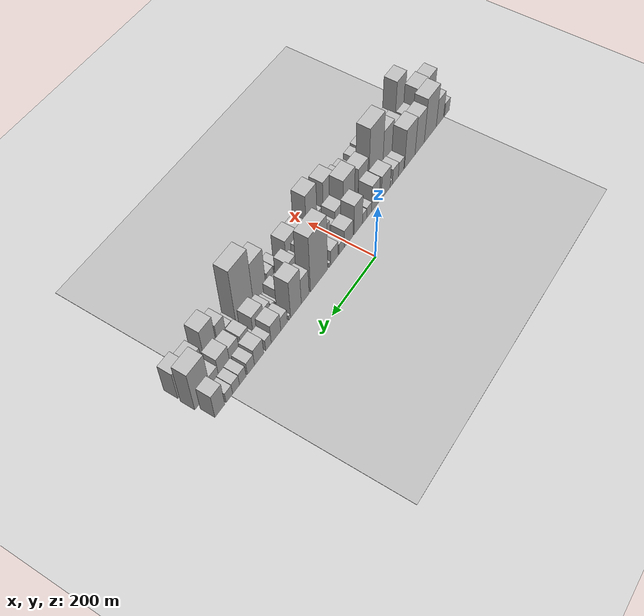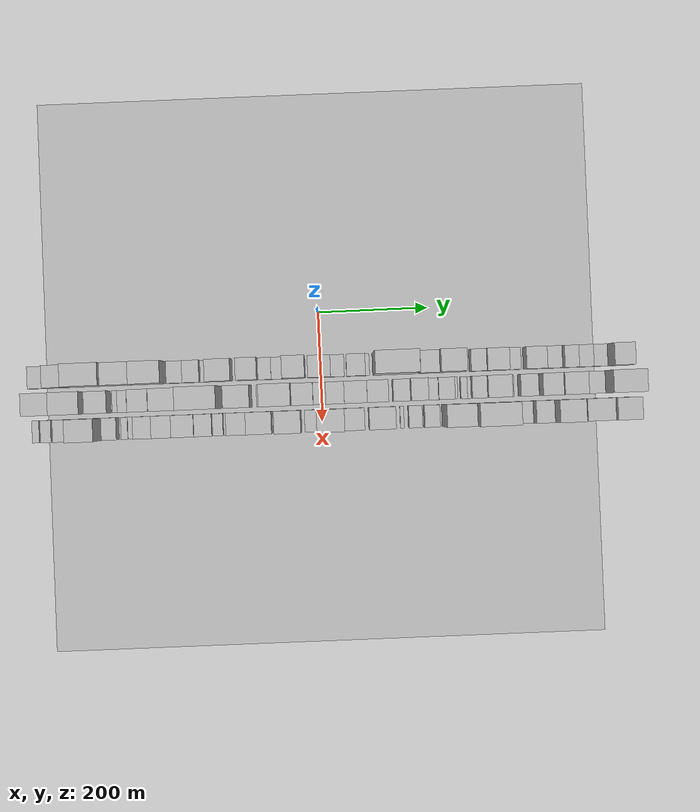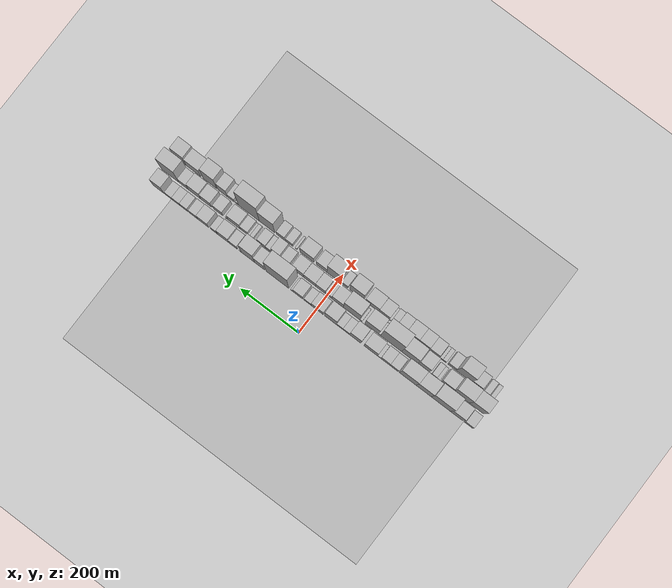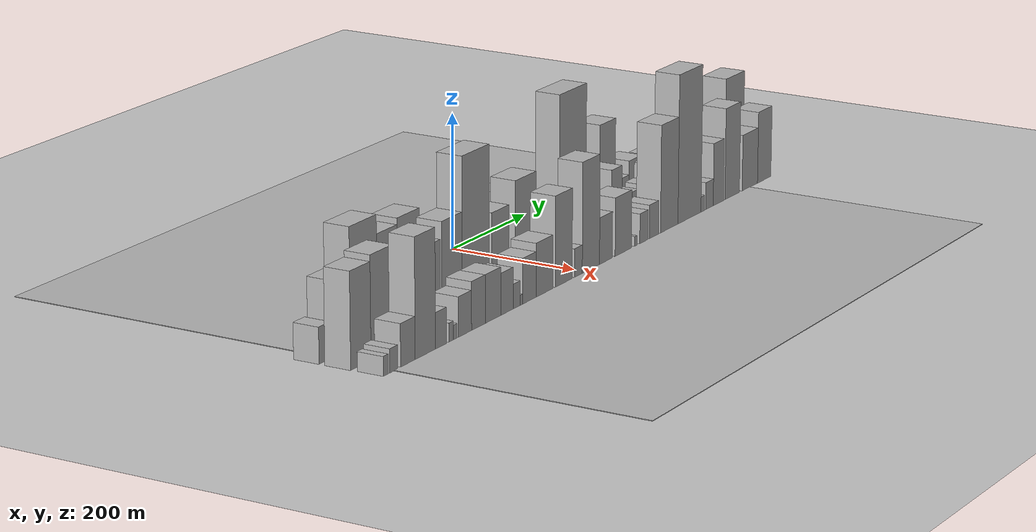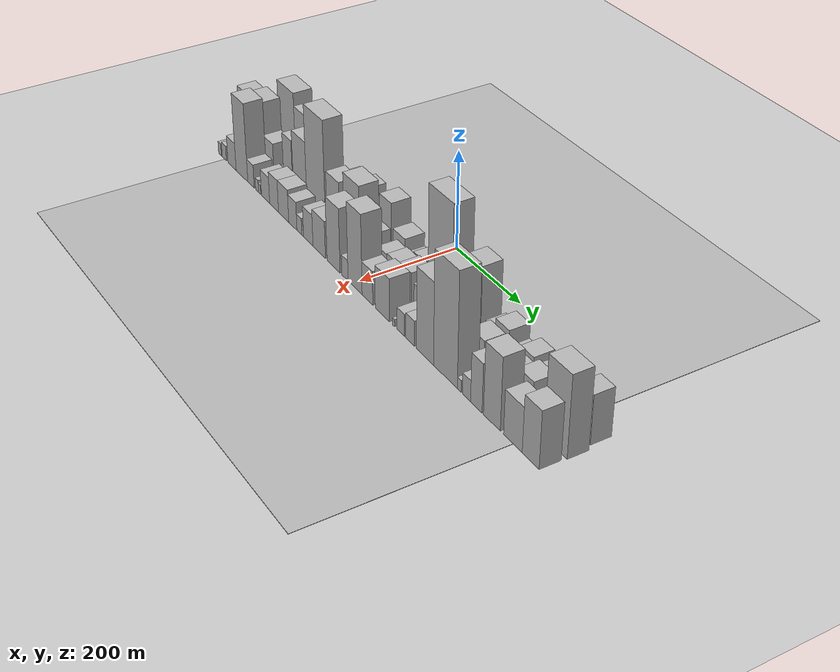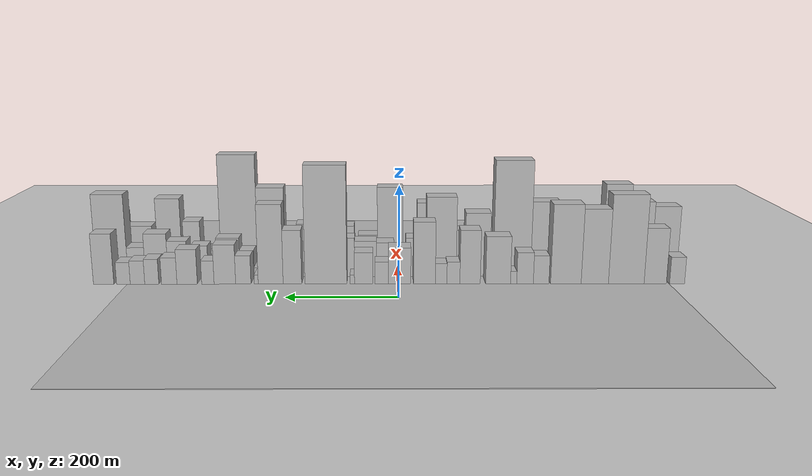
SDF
<?xml version="1.0" encoding="utf-8"?>

<sdf version="1.6">

   <world name="default">

      <gui fullscreen="0">

         <camera name="user_camera">

            <pose>-15 0 4.57585 0 0 0</pose>

            <view_controller>orbit</view_controller>

         </camera>

      </gui>

      <scene>

         <sky>

           <clouds>

             <speed>12</speed>

           </clouds>

         </sky>

         <ambient>0.4 0.4 0.4 1</ambient>

         <background>0.7 0.7 0.7 1</background>

         <shadows>1</shadows>

      </scene>

      <gravity>0 0 -9.8066</gravity>

      <magnetic_field>6e-06 2.3e-05 -4.2e-05</magnetic_field>

      <physics default="0" name="default_physics" type="ode">

         <ode>

            <solver>

               <type>quick</type>

               <iters>10</iters>

               <sor>1.0</sor>

               <use_dynamic_moi_rescaling>0</use_dynamic_moi_rescaling>

            </solver>

            <constraints>

               <cfm>0</cfm>

               <erp>0.2</erp>

               <contact_max_correcting_vel>100</contact_max_correcting_vel>

               <contact_surface_layer>0.001</contact_surface_layer>

            </constraints>

         </ode>

         <max_step_size>0.004</max_step_size>

         <real_time_factor>1</real_time_factor>

         <real_time_update_rate>250</real_time_update_rate>

      </physics>

      <light name="sun" type="directional">

         <cast_shadows>1</cast_shadows>

         <pose>0 0 10 0 0 0</pose>

         <diffuse>0.8 0.8 0.8 1</diffuse>

         <specular>0.2 0.2 0.2 1</specular>

         <attenuation>

            <range>1000</range>

            <constant>0.9</constant>

            <linear>0.01</linear>

            <quadratic>0.001</quadratic>

         </attenuation>

         <direction>-0.5 0.1 -0.9</direction>

      </light>

      <include>

         <name>ground_plane_1</name>

         <uri>model://HANNAS_ground_plane</uri>

         <pose>0 0 0  0 0 0</pose>

      </include>

      <include>

         <name>ground_plane_2</name>

         <uri>model://HANNAS_ground_plane</uri>

         <pose>100 0 0  0 0 0</pose>

      </include>

      <model name="building_1">

         <static>1</static>

         <pose frame="">100.0000 -515.1915 0 0.000000 0.000000 0.000000</pose>

         <link name="link">

            <pose frame="">0 0 25.50 0 0 0</pose>

            <collision name="collision">

               <geometry>

                  <box>

                     <size>40.0000 27.6170 51.0000</size>

                  </box>

               </geometry>

               <max_contacts>10</max_contacts>

               <surface>

                  <contact>

                     <ode/>

                  </contact>

                  <bounce/>

                  <friction>

                     <torsional>

                        <ode/>

                     </torsional>

                     <ode/>

                  </friction>

               </surface>

            </collision>

            <visual name="visual">

               <cast_shadows>0</cast_shadows>

               <geometry>

                  <box>

                     <size>40.0000 27.6170 51.0000</size>

                  </box>

               </geometry>

               <material>

                  <script>

                     <uri>model://HANNAS_wall/materials/scripts</uri>

                     <uri>model://HANNAS_wall/materials/textures</uri>

                     <name>vrc/HANNAS_wall</name>

                  </script>

               </material>

            </visual>

            <self_collide>0</self_collide>

            <enable_wind>0</enable_wind>

            <kinematic>0</kinematic>

         </link>

      </model>

      <model name="building_2">

         <static>1</static>

         <pose frame="">100.0000 -474.7647 0 0.000000 0.000000 0.000000</pose>

         <link name="link">

            <pose frame="">0 0 52.50 0 0 0</pose>

            <collision name="collision">

               <geometry>

                  <box>

                     <size>40.0000 41.2366 105.0000</size>

                  </box>

               </geometry>

               <max_contacts>10</max_contacts>

               <surface>

                  <contact>

                     <ode/>

                  </contact>

                  <bounce/>

                  <friction>

                     <torsional>

                        <ode/>

                     </torsional>

                     <ode/>

                  </friction>

               </surface>

            </collision>

            <visual name="visual">

               <cast_shadows>0</cast_shadows>

               <geometry>

                  <box>

                     <size>40.0000 41.2366 105.0000</size>

                  </box>

               </geometry>

               <material>

                  <script>

                     <uri>model://HANNAS_wall/materials/scripts</uri>

                     <uri>model://HANNAS_wall/materials/textures</uri>

                     <name>vrc/HANNAS_wall</name>

                  </script>

               </material>

            </visual>

            <self_collide>0</self_collide>

            <enable_wind>0</enable_wind>

            <kinematic>0</kinematic>

         </link>

      </model>

      <model name="building_3">

         <static>1</static>

         <pose frame="">100.0000 -421.1329 0 0.000000 0.000000 0.000000</pose>

         <link name="link">

            <pose frame="">0 0 84.00 0 0 0</pose>

            <collision name="collision">

               <geometry>

                  <box>

                     <size>40.0000 66.0271 168.0000</size>

                  </box>

               </geometry>

               <max_contacts>10</max_contacts>

               <surface>

                  <contact>

                     <ode/>

                  </contact>

                  <bounce/>

                  <friction>

                     <torsional>

                        <ode/>

                     </torsional>

                     <ode/>

                  </friction>

               </surface>

            </collision>

            <visual name="visual">

               <cast_shadows>0</cast_shadows>

               <geometry>

                  <box>

                     <size>40.0000 66.0271 168.0000</size>

                  </box>

               </geometry>

               <material>

                  <script>

                     <uri>model://HANNAS_wall/materials/scripts</uri>

                     <uri>model://HANNAS_wall/materials/textures</uri>

                     <name>vrc/HANNAS_wall</name>

                  </script>

               </material>

            </visual>

            <self_collide>0</self_collide>

            <enable_wind>0</enable_wind>

            <kinematic>0</kinematic>

         </link>

      </model>

      <model name="building_4">

         <static>1</static>

         <pose frame="">100.0000 -362.8965 0 0.000000 0.000000 0.000000</pose>

         <link name="link">

            <pose frame="">0 0 70.50 0 0 0</pose>

            <collision name="collision">

               <geometry>

                  <box>

                     <size>40.0000 50.4457 141.0000</size>

                  </box>

               </geometry>

               <max_contacts>10</max_contacts>

               <surface>

                  <contact>

                     <ode/>

                  </contact>

                  <bounce/>

                  <friction>

                     <torsional>

                        <ode/>

                     </torsional>

                     <ode/>

                  </friction>

               </surface>

            </collision>

            <visual name="visual">

               <cast_shadows>0</cast_shadows>

               <geometry>

                  <box>

                     <size>40.0000 50.4457 141.0000</size>

                  </box>

               </geometry>

               <material>

                  <script>

                     <uri>model://HANNAS_wall/materials/scripts</uri>

                     <uri>model://HANNAS_wall/materials/textures</uri>

                     <name>vrc/HANNAS_wall</name>

                  </script>

               </material>

            </visual>

            <self_collide>0</self_collide>

            <enable_wind>0</enable_wind>

            <kinematic>0</kinematic>

         </link>

      </model>

      <model name="building_5">

         <static>1</static>

         <pose frame="">100.0000 -309.4191 0 0.000000 0.000000 0.000000</pose>

         <link name="link">

            <pose frame="">0 0 75.00 0 0 0</pose>

            <collision name="collision">

               <geometry>

                  <box>

                     <size>40.0000 56.5090 150.0000</size>

                  </box>

               </geometry>

               <max_contacts>10</max_contacts>

               <surface>

                  <contact>

                     <ode/>

                  </contact>

                  <bounce/>

                  <friction>

                     <torsional>

                        <ode/>

                     </torsional>

                     <ode/>

                  </friction>

               </surface>

            </collision>

            <visual name="visual">

               <cast_shadows>0</cast_shadows>

               <geometry>

                  <box>

                     <size>40.0000 56.5090 150.0000</size>

                  </box>

               </geometry>

               <material>

                  <script>

                     <uri>model://HANNAS_wall/materials/scripts</uri>

                     <uri>model://HANNAS_wall/materials/textures</uri>

                     <name>vrc/HANNAS_wall</name>

                  </script>

               </material>

            </visual>

            <self_collide>0</self_collide>

            <enable_wind>0</enable_wind>

            <kinematic>0</kinematic>

         </link>

      </model>

      <model name="building_6">

         <static>1</static>

         <pose frame="">100.0000 -263.7066 0 0.000000 0.000000 0.000000</pose>

         <link name="link">

            <pose frame="">0 0 27.00 0 0 0</pose>

            <collision name="collision">

               <geometry>

                  <box>

                     <size>40.0000 28.9161 54.0000</size>

                  </box>

               </geometry>

               <max_contacts>10</max_contacts>

               <surface>

                  <contact>

                     <ode/>

                  </contact>

                  <bounce/>

                  <friction>

                     <torsional>

                        <ode/>

                     </torsional>

                     <ode/>

                  </friction>

               </surface>

            </collision>

            <visual name="visual">

               <cast_shadows>0</cast_shadows>

               <geometry>

                  <box>

                     <size>40.0000 28.9161 54.0000</size>

                  </box>

               </geometry>

               <material>

                  <script>

                     <uri>model://HANNAS_wall/materials/scripts</uri>

                     <uri>model://HANNAS_wall/materials/textures</uri>

                     <name>vrc/HANNAS_wall</name>

                  </script>

               </material>

            </visual>

            <self_collide>0</self_collide>

            <enable_wind>0</enable_wind>

            <kinematic>0</kinematic>

         </link>

      </model>

      <model name="building_7">

         <static>1</static>

         <pose frame="">100.0000 -233.9224 0 0.000000 0.000000 0.000000</pose>

         <link name="link">

            <pose frame="">0 0 30.00 0 0 0</pose>

            <collision name="collision">

               <geometry>

                  <box>

                     <size>40.0000 30.6522 60.0000</size>

                  </box>

               </geometry>

               <max_contacts>10</max_contacts>

               <surface>

                  <contact>

                     <ode/>

                  </contact>

                  <bounce/>

                  <friction>

                     <torsional>

                        <ode/>

                     </torsional>

                     <ode/>

                  </friction>

               </surface>

            </collision>

            <visual name="visual">

               <cast_shadows>0</cast_shadows>

               <geometry>

                  <box>

                     <size>40.0000 30.6522 60.0000</size>

                  </box>

               </geometry>

               <material>

                  <script>

                     <uri>model://HANNAS_wall/materials/scripts</uri>

                     <uri>model://HANNAS_wall/materials/textures</uri>

                     <name>vrc/HANNAS_wall</name>

                  </script>

               </material>

            </visual>

            <self_collide>0</self_collide>

            <enable_wind>0</enable_wind>

            <kinematic>0</kinematic>

         </link>

      </model>

      <model name="building_8">

         <static>1</static>

         <pose frame="">100.0000 -212.8381 0 0.000000 0.000000 0.000000</pose>

         <link name="link">

            <pose frame="">0 0 12.00 0 0 0</pose>

            <collision name="collision">

               <geometry>

                  <box>

                     <size>40.0000 11.5164 24.0000</size>

                  </box>

               </geometry>

               <max_contacts>10</max_contacts>

               <surface>

                  <contact>

                     <ode/>

                  </contact>

                  <bounce/>

                  <friction>

                     <torsional>

                        <ode/>

                     </torsional>

                     <ode/>

                  </friction>

               </surface>

            </collision>

            <visual name="visual">

               <cast_shadows>0</cast_shadows>

               <geometry>

                  <box>

                     <size>40.0000 11.5164 24.0000</size>

                  </box>

               </geometry>

               <material>

                  <script>

                     <uri>model://HANNAS_wall/materials/scripts</uri>

                     <uri>model://HANNAS_wall/materials/textures</uri>

                     <name>vrc/HANNAS_wall</name>

                  </script>

               </material>

            </visual>

            <self_collide>0</self_collide>

            <enable_wind>0</enable_wind>

            <kinematic>0</kinematic>

         </link>

      </model>

      <model name="building_9">

         <static>1</static>

         <pose frame="">100.0000 -184.1226 0 0.000000 0.000000 0.000000</pose>

         <link name="link">

            <pose frame="">0 0 45.00 0 0 0</pose>

            <collision name="collision">

               <geometry>

                  <box>

                     <size>40.0000 45.9146 90.0000</size>

                  </box>

               </geometry>

               <max_contacts>10</max_contacts>

               <surface>

                  <contact>

                     <ode/>

                  </contact>

                  <bounce/>

                  <friction>

                     <torsional>

                        <ode/>

                     </torsional>

                     <ode/>

                  </friction>

               </surface>

            </collision>

            <visual name="visual">

               <cast_shadows>0</cast_shadows>

               <geometry>

                  <box>

                     <size>40.0000 45.9146 90.0000</size>

                  </box>

               </geometry>

               <material>

                  <script>

                     <uri>model://HANNAS_wall/materials/scripts</uri>

                     <uri>model://HANNAS_wall/materials/textures</uri>

                     <name>vrc/HANNAS_wall</name>

                  </script>

               </material>

            </visual>

            <self_collide>0</self_collide>

            <enable_wind>0</enable_wind>

            <kinematic>0</kinematic>

         </link>

      </model>

      <model name="building_10">

         <static>1</static>

         <pose frame="">100.0000 -132.3108 0 0.000000 0.000000 0.000000</pose>

         <link name="link">

            <pose frame="">0 0 51.00 0 0 0</pose>

            <collision name="collision">

               <geometry>

                  <box>

                     <size>40.0000 37.7090 102.0000</size>

                  </box>

               </geometry>

               <max_contacts>10</max_contacts>

               <surface>

                  <contact>

                     <ode/>

                  </contact>

                  <bounce/>

                  <friction>

                     <torsional>

                        <ode/>

                     </torsional>

                     <ode/>

                  </friction>

               </surface>

            </collision>

            <visual name="visual">

               <cast_shadows>0</cast_shadows>

               <geometry>

                  <box>

                     <size>40.0000 37.7090 102.0000</size>

                  </box>

               </geometry>

               <material>

                  <script>

                     <uri>model://HANNAS_wall/materials/scripts</uri>

                     <uri>model://HANNAS_wall/materials/textures</uri>

                     <name>vrc/HANNAS_wall</name>

                  </script>

               </material>

            </visual>

            <self_collide>0</self_collide>

            <enable_wind>0</enable_wind>

            <kinematic>0</kinematic>

         </link>

      </model>

      <model name="building_11">

         <static>1</static>

         <pose frame="">100.0000 -101.5084 0 0.000000 0.000000 0.000000</pose>

         <link name="link">

            <pose frame="">0 0 21.00 0 0 0</pose>

            <collision name="collision">

               <geometry>

                  <box>

                     <size>40.0000 23.8957 42.0000</size>

                  </box>

               </geometry>

               <max_contacts>10</max_contacts>

               <surface>

                  <contact>

                     <ode/>

                  </contact>

                  <bounce/>

                  <friction>

                     <torsional>

                        <ode/>

                     </torsional>

                     <ode/>

                  </friction>

               </surface>

            </collision>

            <visual name="visual">

               <cast_shadows>0</cast_shadows>

               <geometry>

                  <box>

                     <size>40.0000 23.8957 42.0000</size>

                  </box>

               </geometry>

               <material>

                  <script>

                     <uri>model://HANNAS_wall/materials/scripts</uri>

                     <uri>model://HANNAS_wall/materials/textures</uri>

                     <name>vrc/HANNAS_wall</name>

                  </script>

               </material>

            </visual>

            <self_collide>0</self_collide>

            <enable_wind>0</enable_wind>

            <kinematic>0</kinematic>

         </link>

      </model>

      <model name="building_12">

         <static>1</static>

         <pose frame="">100.0000 -78.9548 0 0.000000 0.000000 0.000000</pose>

         <link name="link">

            <pose frame="">0 0 19.50 0 0 0</pose>

            <collision name="collision">

               <geometry>

                  <box>

                     <size>40.0000 21.2116 39.0000</size>

                  </box>

               </geometry>

               <max_contacts>10</max_contacts>

               <surface>

                  <contact>

                     <ode/>

                  </contact>

                  <bounce/>

                  <friction>

                     <torsional>

                        <ode/>

                     </torsional>

                     <ode/>

                  </friction>

               </surface>

            </collision>

            <visual name="visual">

               <cast_shadows>0</cast_shadows>

               <geometry>

                  <box>

                     <size>40.0000 21.2116 39.0000</size>

                  </box>

               </geometry>

               <material>

                  <script>

                     <uri>model://HANNAS_wall/materials/scripts</uri>

                     <uri>model://HANNAS_wall/materials/textures</uri>

                     <name>vrc/HANNAS_wall</name>

                  </script>

               </material>

            </visual>

            <self_collide>0</self_collide>

            <enable_wind>0</enable_wind>

            <kinematic>0</kinematic>

         </link>

      </model>

      <model name="building_13">

         <static>1</static>

         <pose frame="">100.0000 -48.1221 0 0.000000 0.000000 0.000000</pose>

         <link name="link">

            <pose frame="">0 0 58.50 0 0 0</pose>

            <collision name="collision">

               <geometry>

                  <box>

                     <size>40.0000 40.4538 117.0000</size>

                  </box>

               </geometry>

               <max_contacts>10</max_contacts>

               <surface>

                  <contact>

                     <ode/>

                  </contact>

                  <bounce/>

                  <friction>

                     <torsional>

                        <ode/>

                     </torsional>

                     <ode/>

                  </friction>

               </surface>

            </collision>

            <visual name="visual">

               <cast_shadows>0</cast_shadows>

               <geometry>

                  <box>

                     <size>40.0000 40.4538 117.0000</size>

                  </box>

               </geometry>

               <material>

                  <script>

                     <uri>model://HANNAS_wall/materials/scripts</uri>

                     <uri>model://HANNAS_wall/materials/textures</uri>

                     <name>vrc/HANNAS_wall</name>

                  </script>

               </material>

            </visual>

            <self_collide>0</self_collide>

            <enable_wind>0</enable_wind>

            <kinematic>0</kinematic>

         </link>

      </model>

      <model name="building_14">

         <static>1</static>

         <pose frame="">100.0000 -2.3943 0 0.000000 0.000000 0.000000</pose>

         <link name="link">

            <pose frame="">0 0 34.50 0 0 0</pose>

            <collision name="collision">

               <geometry>

                  <box>

                     <size>40.0000 41.0018 69.0000</size>

                  </box>

               </geometry>

               <max_contacts>10</max_contacts>

               <surface>

                  <contact>

                     <ode/>

                  </contact>

                  <bounce/>

                  <friction>

                     <torsional>

                        <ode/>

                     </torsional>

                     <ode/>

                  </friction>

               </surface>

            </collision>

            <visual name="visual">

               <cast_shadows>0</cast_shadows>

               <geometry>

                  <box>

                     <size>40.0000 41.0018 69.0000</size>

                  </box>

               </geometry>

               <material>

                  <script>

                     <uri>model://HANNAS_wall/materials/scripts</uri>

                     <uri>model://HANNAS_wall/materials/textures</uri>

                     <name>vrc/HANNAS_wall</name>

                  </script>

               </material>

            </visual>

            <self_collide>0</self_collide>

            <enable_wind>0</enable_wind>

            <kinematic>0</kinematic>

         </link>

      </model>

      <model name="building_15">

         <static>1</static>

         <pose frame="">100.0000 30.6435 0 0.000000 0.000000 0.000000</pose>

         <link name="link">

            <pose frame="">0 0 21.00 0 0 0</pose>

            <collision name="collision">

               <geometry>

                  <box>

                     <size>40.0000 25.0737 42.0000</size>

                  </box>

               </geometry>

               <max_contacts>10</max_contacts>

               <surface>

                  <contact>

                     <ode/>

                  </contact>

                  <bounce/>

                  <friction>

                     <torsional>

                        <ode/>

                     </torsional>

                     <ode/>

                  </friction>

               </surface>

            </collision>

            <visual name="visual">

               <cast_shadows>0</cast_shadows>

               <geometry>

                  <box>

                     <size>40.0000 25.0737 42.0000</size>

                  </box>

               </geometry>

               <material>

                  <script>

                     <uri>model://HANNAS_wall/materials/scripts</uri>

                     <uri>model://HANNAS_wall/materials/textures</uri>

                     <name>vrc/HANNAS_wall</name>

                  </script>

               </material>

            </visual>

            <self_collide>0</self_collide>

            <enable_wind>0</enable_wind>

            <kinematic>0</kinematic>

         </link>

      </model>

      <model name="building_16">

         <static>1</static>

         <pose frame="">100.0000 64.1118 0 0.000000 0.000000 0.000000</pose>

         <link name="link">

            <pose frame="">0 0 30.00 0 0 0</pose>

            <collision name="collision">

               <geometry>

                  <box>

                     <size>40.0000 33.8629 60.0000</size>

                  </box>

               </geometry>

               <max_contacts>10</max_contacts>

               <surface>

                  <contact>

                     <ode/>

                  </contact>

                  <bounce/>

                  <friction>

                     <torsional>

                        <ode/>

                     </torsional>

                     <ode/>

                  </friction>

               </surface>

            </collision>

            <visual name="visual">

               <cast_shadows>0</cast_shadows>

               <geometry>

                  <box>

                     <size>40.0000 33.8629 60.0000</size>

                  </box>

               </geometry>

               <material>

                  <script>

                     <uri>model://HANNAS_wall/materials/scripts</uri>

                     <uri>model://HANNAS_wall/materials/textures</uri>

                     <name>vrc/HANNAS_wall</name>

                  </script>

               </material>

            </visual>

            <self_collide>0</self_collide>

            <enable_wind>0</enable_wind>

            <kinematic>0</kinematic>

         </link>

      </model>

      <model name="building_17">

         <static>1</static>

         <pose frame="">100.0000 85.1269 0 0.000000 0.000000 0.000000</pose>

         <link name="link">

            <pose frame="">0 0 9.00 0 0 0</pose>

            <collision name="collision">

               <geometry>

                  <box>

                     <size>40.0000 8.1673 18.0000</size>

                  </box>

               </geometry>

               <max_contacts>10</max_contacts>

               <surface>

                  <contact>

                     <ode/>

                  </contact>

                  <bounce/>

                  <friction>

                     <torsional>

                        <ode/>

                     </torsional>

                     <ode/>

                  </friction>

               </surface>

            </collision>

            <visual name="visual">

               <cast_shadows>0</cast_shadows>

               <geometry>

                  <box>

                     <size>40.0000 8.1673 18.0000</size>

                  </box>

               </geometry>

               <material>

                  <script>

                     <uri>model://HANNAS_wall/materials/scripts</uri>

                     <uri>model://HANNAS_wall/materials/textures</uri>

                     <name>vrc/HANNAS_wall</name>

                  </script>

               </material>

            </visual>

            <self_collide>0</self_collide>

            <enable_wind>0</enable_wind>

            <kinematic>0</kinematic>

         </link>

      </model>

      <model name="building_18">

         <static>1</static>

         <pose frame="">100.0000 133.8508 0 0.000000 0.000000 0.000000</pose>

         <link name="link">

            <pose frame="">0 0 111.00 0 0 0</pose>

            <collision name="collision">

               <geometry>

                  <box>

                     <size>40.0000 77.2806 222.0000</size>

                  </box>

               </geometry>

               <max_contacts>10</max_contacts>

               <surface>

                  <contact>

                     <ode/>

                  </contact>

                  <bounce/>

                  <friction>

                     <torsional>

                        <ode/>

                     </torsional>

                     <ode/>

                  </friction>

               </surface>

            </collision>

            <visual name="visual">

               <cast_shadows>0</cast_shadows>

               <geometry>

                  <box>

                     <size>40.0000 77.2806 222.0000</size>

                  </box>

               </geometry>

               <material>

                  <script>

                     <uri>model://HANNAS_wall/materials/scripts</uri>

                     <uri>model://HANNAS_wall/materials/textures</uri>

                     <name>vrc/HANNAS_wall</name>

                  </script>

               </material>

            </visual>

            <self_collide>0</self_collide>

            <enable_wind>0</enable_wind>

            <kinematic>0</kinematic>

         </link>

      </model>

      <model name="building_19">

         <static>1</static>

         <pose frame="">100.0000 195.5853 0 0.000000 0.000000 0.000000</pose>

         <link name="link">

            <pose frame="">0 0 51.00 0 0 0</pose>

            <collision name="collision">

               <geometry>

                  <box>

                     <size>40.0000 34.1883 102.0000</size>

                  </box>

               </geometry>

               <max_contacts>10</max_contacts>

               <surface>

                  <contact>

                     <ode/>

                  </contact>

                  <bounce/>

                  <friction>

                     <torsional>

                        <ode/>

                     </torsional>

                     <ode/>

                  </friction>

               </surface>

            </collision>

            <visual name="visual">

               <cast_shadows>0</cast_shadows>

               <geometry>

                  <box>

                     <size>40.0000 34.1883 102.0000</size>

                  </box>

               </geometry>

               <material>

                  <script>

                     <uri>model://HANNAS_wall/materials/scripts</uri>

                     <uri>model://HANNAS_wall/materials/textures</uri>

                     <name>vrc/HANNAS_wall</name>

                  </script>

               </material>

            </visual>

            <self_collide>0</self_collide>

            <enable_wind>0</enable_wind>

            <kinematic>0</kinematic>

         </link>

      </model>

      <model name="building_20">

         <static>1</static>

         <pose frame="">100.0000 235.7019 0 0.000000 0.000000 0.000000</pose>

         <link name="link">

            <pose frame="">0 0 75.00 0 0 0</pose>

            <collision name="collision">

               <geometry>

                  <box>

                     <size>40.0000 46.0451 150.0000</size>

                  </box>

               </geometry>

               <max_contacts>10</max_contacts>

               <surface>

                  <contact>

                     <ode/>

                  </contact>

                  <bounce/>

                  <friction>

                     <torsional>

                        <ode/>

                     </torsional>

                     <ode/>

                  </friction>

               </surface>

            </collision>

            <visual name="visual">

               <cast_shadows>0</cast_shadows>

               <geometry>

                  <box>

                     <size>40.0000 46.0451 150.0000</size>

                  </box>

               </geometry>

               <material>

                  <script>

                     <uri>model://HANNAS_wall/materials/scripts</uri>

                     <uri>model://HANNAS_wall/materials/textures</uri>

                     <name>vrc/HANNAS_wall</name>

                  </script>

               </material>

            </visual>

            <self_collide>0</self_collide>

            <enable_wind>0</enable_wind>

            <kinematic>0</kinematic>

         </link>

      </model>

      <model name="building_21">

         <static>1</static>

         <pose frame="">100.0000 262.3611 0 0.000000 0.000000 0.000000</pose>

         <link name="link">

            <pose frame="">0 0 9.00 0 0 0</pose>

            <collision name="collision">

               <geometry>

                  <box>

                     <size>40.0000 7.2733 18.0000</size>

                  </box>

               </geometry>

               <max_contacts>10</max_contacts>

               <surface>

                  <contact>

                     <ode/>

                  </contact>

                  <bounce/>

                  <friction>

                     <torsional>

                        <ode/>

                     </torsional>

                     <ode/>

                  </friction>

               </surface>

            </collision>

            <visual name="visual">

               <cast_shadows>0</cast_shadows>

               <geometry>

                  <box>

                     <size>40.0000 7.2733 18.0000</size>

                  </box>

               </geometry>

               <material>

                  <script>

                     <uri>model://HANNAS_wall/materials/scripts</uri>

                     <uri>model://HANNAS_wall/materials/textures</uri>

                     <name>vrc/HANNAS_wall</name>

                  </script>

               </material>

            </visual>

            <self_collide>0</self_collide>

            <enable_wind>0</enable_wind>

            <kinematic>0</kinematic>

         </link>

      </model>

      <model name="building_22">

         <static>1</static>

         <pose frame="">100.0000 286.1482 0 0.000000 0.000000 0.000000</pose>

         <link name="link">

            <pose frame="">0 0 27.00 0 0 0</pose>

            <collision name="collision">

               <geometry>

                  <box>

                     <size>40.0000 28.3007 54.0000</size>

                  </box>

               </geometry>

               <max_contacts>10</max_contacts>

               <surface>

                  <contact>

                     <ode/>

                  </contact>

                  <bounce/>

                  <friction>

                     <torsional>

                        <ode/>

                     </torsional>

                     <ode/>

                  </friction>

               </surface>

            </collision>

            <visual name="visual">

               <cast_shadows>0</cast_shadows>

               <geometry>

                  <box>

                     <size>40.0000 28.3007 54.0000</size>

                  </box>

               </geometry>

               <material>

                  <script>

                     <uri>model://HANNAS_wall/materials/scripts</uri>

                     <uri>model://HANNAS_wall/materials/textures</uri>

                     <name>vrc/HANNAS_wall</name>

                  </script>

               </material>

            </visual>

            <self_collide>0</self_collide>

            <enable_wind>0</enable_wind>

            <kinematic>0</kinematic>

         </link>

      </model>

      <model name="building_23">

         <static>1</static>

         <pose frame="">100.0000 320.1502 0 0.000000 0.000000 0.000000</pose>

         <link name="link">

            <pose frame="">0 0 37.50 0 0 0</pose>

            <collision name="collision">

               <geometry>

                  <box>

                     <size>40.0000 39.7032 75.0000</size>

                  </box>

               </geometry>

               <max_contacts>10</max_contacts>

               <surface>

                  <contact>

                     <ode/>

                  </contact>

                  <bounce/>

                  <friction>

                     <torsional>

                        <ode/>

                     </torsional>

                     <ode/>

                  </friction>

               </surface>

            </collision>

            <visual name="visual">

               <cast_shadows>0</cast_shadows>

               <geometry>

                  <box>

                     <size>40.0000 39.7032 75.0000</size>

                  </box>

               </geometry>

               <material>

                  <script>

                     <uri>model://HANNAS_wall/materials/scripts</uri>

                     <uri>model://HANNAS_wall/materials/textures</uri>

                     <name>vrc/HANNAS_wall</name>

                  </script>

               </material>

            </visual>

            <self_collide>0</self_collide>

            <enable_wind>0</enable_wind>

            <kinematic>0</kinematic>

         </link>

      </model>

      <model name="building_24">

         <static>1</static>

         <pose frame="">100.0000 351.4448 0 0.000000 0.000000 0.000000</pose>

         <link name="link">

            <pose frame="">0 0 22.50 0 0 0</pose>

            <collision name="collision">

               <geometry>

                  <box>

                     <size>40.0000 22.8860 45.0000</size>

                  </box>

               </geometry>

               <max_contacts>10</max_contacts>

               <surface>

                  <contact>

                     <ode/>

                  </contact>

                  <bounce/>

                  <friction>

                     <torsional>

                        <ode/>

                     </torsional>

                     <ode/>

                  </friction>

               </surface>

            </collision>

            <visual name="visual">

               <cast_shadows>0</cast_shadows>

               <geometry>

                  <box>

                     <size>40.0000 22.8860 45.0000</size>

                  </box>

               </geometry>

               <material>

                  <script>

                     <uri>model://HANNAS_wall/materials/scripts</uri>

                     <uri>model://HANNAS_wall/materials/textures</uri>

                     <name>vrc/HANNAS_wall</name>

                  </script>

               </material>

            </visual>

            <self_collide>0</self_collide>

            <enable_wind>0</enable_wind>

            <kinematic>0</kinematic>

         </link>

      </model>

      <model name="building_25">

         <static>1</static>

         <pose frame="">100.0000 389.6621 0 0.000000 0.000000 0.000000</pose>

         <link name="link">

            <pose frame="">0 0 33.00 0 0 0</pose>

            <collision name="collision">

               <geometry>

                  <box>

                     <size>40.0000 37.5485 66.0000</size>

                  </box>

               </geometry>

               <max_contacts>10</max_contacts>

               <surface>

                  <contact>

                     <ode/>

                  </contact>

                  <bounce/>

                  <friction>

                     <torsional>

                        <ode/>

                     </torsional>

                     <ode/>

                  </friction>

               </surface>

            </collision>

            <visual name="visual">

               <cast_shadows>0</cast_shadows>

               <geometry>

                  <box>

                     <size>40.0000 37.5485 66.0000</size>

                  </box>

               </geometry>

               <material>

                  <script>

                     <uri>model://HANNAS_wall/materials/scripts</uri>

                     <uri>model://HANNAS_wall/materials/textures</uri>

                     <name>vrc/HANNAS_wall</name>

                  </script>

               </material>

            </visual>

            <self_collide>0</self_collide>

            <enable_wind>0</enable_wind>

            <kinematic>0</kinematic>

         </link>

      </model>

      <model name="building_26">

         <static>1</static>

         <pose frame="">100.0000 422.6355 0 0.000000 0.000000 0.000000</pose>

         <link name="link">

            <pose frame="">0 0 25.50 0 0 0</pose>

            <collision name="collision">

               <geometry>

                  <box>

                     <size>40.0000 28.3984 51.0000</size>

                  </box>

               </geometry>

               <max_contacts>10</max_contacts>

               <surface>

                  <contact>

                     <ode/>

                  </contact>

                  <bounce/>

                  <friction>

                     <torsional>

                        <ode/>

                     </torsional>

                     <ode/>

                  </friction>

               </surface>

            </collision>

            <visual name="visual">

               <cast_shadows>0</cast_shadows>

               <geometry>

                  <box>

                     <size>40.0000 28.3984 51.0000</size>

                  </box>

               </geometry>

               <material>

                  <script>

                     <uri>model://HANNAS_wall/materials/scripts</uri>

                     <uri>model://HANNAS_wall/materials/textures</uri>

                     <name>vrc/HANNAS_wall</name>

                  </script>

               </material>

            </visual>

            <self_collide>0</self_collide>

            <enable_wind>0</enable_wind>

            <kinematic>0</kinematic>

         </link>

      </model>

      <model name="building_27">

         <static>1</static>

         <pose frame="">100.0000 454.8215 0 0.000000 0.000000 0.000000</pose>

         <link name="link">

            <pose frame="">0 0 24.00 0 0 0</pose>

            <collision name="collision">

               <geometry>

                  <box>

                     <size>40.0000 25.9734 48.0000</size>

                  </box>

               </geometry>

               <max_contacts>10</max_contacts>

               <surface>

                  <contact>

                     <ode/>

                  </contact>

                  <bounce/>

                  <friction>

                     <torsional>

                        <ode/>

                     </torsional>

                     <ode/>

                  </friction>

               </surface>

            </collision>

            <visual name="visual">

               <cast_shadows>0</cast_shadows>

               <geometry>

                  <box>

                     <size>40.0000 25.9734 48.0000</size>

                  </box>

               </geometry>

               <material>

                  <script>

                     <uri>model://HANNAS_wall/materials/scripts</uri>

                     <uri>model://HANNAS_wall/materials/textures</uri>

                     <name>vrc/HANNAS_wall</name>

                  </script>

               </material>

            </visual>

            <self_collide>0</self_collide>

            <enable_wind>0</enable_wind>

            <kinematic>0</kinematic>

         </link>

      </model>

      <model name="building_28">

         <static>1</static>

         <pose frame="">100.0000 481.1460 0 0.000000 0.000000 0.000000</pose>

         <link name="link">

            <pose frame="">0 0 22.50 0 0 0</pose>

            <collision name="collision">

               <geometry>

                  <box>

                     <size>40.0000 26.6757 45.0000</size>

                  </box>

               </geometry>

               <max_contacts>10</max_contacts>

               <surface>

                  <contact>

                     <ode/>

                  </contact>

                  <bounce/>

                  <friction>

                     <torsional>

                        <ode/>

                     </torsional>

                     <ode/>

                  </friction>

               </surface>

            </collision>

            <visual name="visual">

               <cast_shadows>0</cast_shadows>

               <geometry>

                  <box>

                     <size>40.0000 26.6757 45.0000</size>

                  </box>

               </geometry>

               <material>

                  <script>

                     <uri>model://HANNAS_wall/materials/scripts</uri>

                     <uri>model://HANNAS_wall/materials/textures</uri>

                     <name>vrc/HANNAS_wall</name>

                  </script>

               </material>

            </visual>

            <self_collide>0</self_collide>

            <enable_wind>0</enable_wind>

            <kinematic>0</kinematic>

         </link>

      </model>

      <model name="building_29">

         <static>1</static>

         <pose frame="">100.0000 507.0829 0 0.000000 0.000000 0.000000</pose>

         <link name="link">

            <pose frame="">0 0 21.00 0 0 0</pose>

            <collision name="collision">

               <geometry>

                  <box>

                     <size>40.0000 25.1980 42.0000</size>

                  </box>

               </geometry>

               <max_contacts>10</max_contacts>

               <surface>

                  <contact>

                     <ode/>

                  </contact>

                  <bounce/>

                  <friction>

                     <torsional>

                        <ode/>

                     </torsional>

                     <ode/>

                  </friction>

               </surface>

            </collision>

            <visual name="visual">

               <cast_shadows>0</cast_shadows>

               <geometry>

                  <box>

                     <size>40.0000 25.1980 42.0000</size>

                  </box>

               </geometry>

               <material>

                  <script>

                     <uri>model://HANNAS_wall/materials/scripts</uri>

                     <uri>model://HANNAS_wall/materials/textures</uri>

                     <name>vrc/HANNAS_wall</name>

                  </script>

               </material>

            </visual>

            <self_collide>0</self_collide>

            <enable_wind>0</enable_wind>

            <kinematic>0</kinematic>

         </link>

      </model>

      <model name="building_30">

         <static>1</static>

         <pose frame="">100.0000 543.4878 0 0.000000 0.000000 0.000000</pose>

         <link name="link">

            <pose frame="">0 0 48.00 0 0 0</pose>

            <collision name="collision">

               <geometry>

                  <box>

                     <size>40.0000 37.6117 96.0000</size>

                  </box>

               </geometry>

               <max_contacts>10</max_contacts>

               <surface>

                  <contact>

                     <ode/>

                  </contact>

                  <bounce/>

                  <friction>

                     <torsional>

                        <ode/>

                     </torsional>

                     <ode/>

                  </friction>

               </surface>

            </collision>

            <visual name="visual">

               <cast_shadows>0</cast_shadows>

               <geometry>

                  <box>

                     <size>40.0000 37.6117 96.0000</size>

                  </box>

               </geometry>

               <material>

                  <script>

                     <uri>model://HANNAS_wall/materials/scripts</uri>

                     <uri>model://HANNAS_wall/materials/textures</uri>

                     <name>vrc/HANNAS_wall</name>

                  </script>

               </material>

            </visual>

            <self_collide>0</self_collide>

            <enable_wind>0</enable_wind>

            <kinematic>0</kinematic>

         </link>

      </model>

      <model name="building_31">

         <static>1</static>

         <pose frame="">149.0000 -504.5442 0 0.000000 0.000000 0.000000</pose>

         <link name="link">

            <pose frame="">0 0 67.50 0 0 0</pose>

            <collision name="collision">

               <geometry>

                  <box>

                     <size>40.0000 48.9116 135.0000</size>

                  </box>

               </geometry>

               <max_contacts>10</max_contacts>

               <surface>

                  <contact>

                     <ode/>

                  </contact>

                  <bounce/>

                  <friction>

                     <torsional>

                        <ode/>

                     </torsional>

                     <ode/>

                  </friction>

               </surface>

            </collision>

            <visual name="visual">

               <cast_shadows>0</cast_shadows>

               <geometry>

                  <box>

                     <size>40.0000 48.9116 135.0000</size>

                  </box>

               </geometry>

               <material>

                  <script>

                     <uri>model://HANNAS_wall/materials/scripts</uri>

                     <uri>model://HANNAS_wall/materials/textures</uri>

                     <name>vrc/HANNAS_wall</name>

                  </script>

               </material>

            </visual>

            <self_collide>0</self_collide>

            <enable_wind>0</enable_wind>

            <kinematic>0</kinematic>

         </link>

      </model>

      <model name="building_32">

         <static>1</static>

         <pose frame="">149.0000 -453.0408 0 0.000000 0.000000 0.000000</pose>

         <link name="link">

            <pose frame="">0 0 72.00 0 0 0</pose>

            <collision name="collision">

               <geometry>

                  <box>

                     <size>40.0000 54.0952 144.0000</size>

                  </box>

               </geometry>

               <max_contacts>10</max_contacts>

               <surface>

                  <contact>

                     <ode/>

                  </contact>

                  <bounce/>

                  <friction>

                     <torsional>

                        <ode/>

                     </torsional>

                     <ode/>

                  </friction>

               </surface>

            </collision>

            <visual name="visual">

               <cast_shadows>0</cast_shadows>

               <geometry>

                  <box>

                     <size>40.0000 54.0952 144.0000</size>

                  </box>

               </geometry>

               <material>

                  <script>

                     <uri>model://HANNAS_wall/materials/scripts</uri>

                     <uri>model://HANNAS_wall/materials/textures</uri>

                     <name>vrc/HANNAS_wall</name>

                  </script>

               </material>

            </visual>

            <self_collide>0</self_collide>

            <enable_wind>0</enable_wind>

            <kinematic>0</kinematic>

         </link>

      </model>

      <model name="building_33">

         <static>1</static>

         <pose frame="">149.0000 -405.5895 0 0.000000 0.000000 0.000000</pose>

         <link name="link">

            <pose frame="">0 0 37.50 0 0 0</pose>

            <collision name="collision">

               <geometry>

                  <box>

                     <size>40.0000 40.8075 75.0000</size>

                  </box>

               </geometry>

               <max_contacts>10</max_contacts>

               <surface>

                  <contact>

                     <ode/>

                  </contact>

                  <bounce/>

                  <friction>

                     <torsional>

                        <ode/>

                     </torsional>

                     <ode/>

                  </friction>

               </surface>

            </collision>

            <visual name="visual">

               <cast_shadows>0</cast_shadows>

               <geometry>

                  <box>

                     <size>40.0000 40.8075 75.0000</size>

                  </box>

               </geometry>

               <material>

                  <script>

                     <uri>model://HANNAS_wall/materials/scripts</uri>

                     <uri>model://HANNAS_wall/materials/textures</uri>

                     <name>vrc/HANNAS_wall</name>

                  </script>

               </material>

            </visual>

            <self_collide>0</self_collide>

            <enable_wind>0</enable_wind>

            <kinematic>0</kinematic>

         </link>

      </model>

      <model name="building_34">

         <static>1</static>

         <pose frame="">149.0000 -375.9434 0 0.000000 0.000000 0.000000</pose>

         <link name="link">

            <pose frame="">0 0 10.50 0 0 0</pose>

            <collision name="collision">

               <geometry>

                  <box>

                     <size>40.0000 10.4847 21.0000</size>

                  </box>

               </geometry>

               <max_contacts>10</max_contacts>

               <surface>

                  <contact>

                     <ode/>

                  </contact>

                  <bounce/>

                  <friction>

                     <torsional>

                        <ode/>

                     </torsional>

                     <ode/>

                  </friction>

               </surface>

            </collision>

            <visual name="visual">

               <cast_shadows>0</cast_shadows>

               <geometry>

                  <box>

                     <size>40.0000 10.4847 21.0000</size>

                  </box>

               </geometry>

               <material>

                  <script>

                     <uri>model://HANNAS_wall/materials/scripts</uri>

                     <uri>model://HANNAS_wall/materials/textures</uri>

                     <name>vrc/HANNAS_wall</name>

                  </script>

               </material>

            </visual>

            <self_collide>0</self_collide>

            <enable_wind>0</enable_wind>

            <kinematic>0</kinematic>

         </link>

      </model>

      <model name="building_35">

         <static>1</static>

         <pose frame="">149.0000 -362.0849 0 0.000000 0.000000 0.000000</pose>

         <link name="link">

            <pose frame="">0 0 16.50 0 0 0</pose>

            <collision name="collision">

               <geometry>

                  <box>

                     <size>40.0000 17.2323 33.0000</size>

                  </box>

               </geometry>

               <max_contacts>10</max_contacts>

               <surface>

                  <contact>

                     <ode/>

                  </contact>

                  <bounce/>

                  <friction>

                     <torsional>

                        <ode/>

                     </torsional>

                     <ode/>

                  </friction>

               </surface>

            </collision>

            <visual name="visual">

               <cast_shadows>0</cast_shadows>

               <geometry>

                  <box>

                     <size>40.0000 17.2323 33.0000</size>

                  </box>

               </geometry>

               <material>

                  <script>

                     <uri>model://HANNAS_wall/materials/scripts</uri>

                     <uri>model://HANNAS_wall/materials/textures</uri>

                     <name>vrc/HANNAS_wall</name>

                  </script>

               </material>

            </visual>

            <self_collide>0</self_collide>

            <enable_wind>0</enable_wind>

            <kinematic>0</kinematic>

         </link>

      </model>

      <model name="building_36">

         <static>1</static>

         <pose frame="">149.0000 -325.2871 0 0.000000 0.000000 0.000000</pose>

         <link name="link">

            <pose frame="">0 0 60.00 0 0 0</pose>

            <collision name="collision">

               <geometry>

                  <box>

                     <size>40.0000 36.3631 120.0000</size>

                  </box>

               </geometry>

               <max_contacts>10</max_contacts>

               <surface>

                  <contact>

                     <ode/>

                  </contact>

                  <bounce/>

                  <friction>

                     <torsional>

                        <ode/>

                     </torsional>

                     <ode/>

                  </friction>

               </surface>

            </collision>

            <visual name="visual">

               <cast_shadows>0</cast_shadows>

               <geometry>

                  <box>

                     <size>40.0000 36.3631 120.0000</size>

                  </box>

               </geometry>

               <material>

                  <script>

                     <uri>model://HANNAS_wall/materials/scripts</uri>

                     <uri>model://HANNAS_wall/materials/textures</uri>

                     <name>vrc/HANNAS_wall</name>

                  </script>

               </material>

            </visual>

            <self_collide>0</self_collide>

            <enable_wind>0</enable_wind>

            <kinematic>0</kinematic>

         </link>

      </model>

      <model name="building_37">

         <static>1</static>

         <pose frame="">149.0000 -277.8152 0 0.000000 0.000000 0.000000</pose>

         <link name="link">

            <pose frame="">0 0 72.00 0 0 0</pose>

            <collision name="collision">

               <geometry>

                  <box>

                     <size>40.0000 52.5809 144.0000</size>

                  </box>

               </geometry>

               <max_contacts>10</max_contacts>

               <surface>

                  <contact>

                     <ode/>

                  </contact>

                  <bounce/>

                  <friction>

                     <torsional>

                        <ode/>

                     </torsional>

                     <ode/>

                  </friction>

               </surface>

            </collision>

            <visual name="visual">

               <cast_shadows>0</cast_shadows>

               <geometry>

                  <box>

                     <size>40.0000 52.5809 144.0000</size>

                  </box>

               </geometry>

               <material>

                  <script>

                     <uri>model://HANNAS_wall/materials/scripts</uri>

                     <uri>model://HANNAS_wall/materials/textures</uri>

                     <name>vrc/HANNAS_wall</name>

                  </script>

               </material>

            </visual>

            <self_collide>0</self_collide>

            <enable_wind>0</enable_wind>

            <kinematic>0</kinematic>

         </link>

      </model>

      <model name="building_38">

         <static>1</static>

         <pose frame="">149.0000 -216.0042 0 0.000000 0.000000 0.000000</pose>

         <link name="link">

            <pose frame="">0 0 111.00 0 0 0</pose>

            <collision name="collision">

               <geometry>

                  <box>

                     <size>40.0000 71.0410 222.0000</size>

                  </box>

               </geometry>

               <max_contacts>10</max_contacts>

               <surface>

                  <contact>

                     <ode/>

                  </contact>

                  <bounce/>

                  <friction>

                     <torsional>

                        <ode/>

                     </torsional>

                     <ode/>

                  </friction>

               </surface>

            </collision>

            <visual name="visual">

               <cast_shadows>0</cast_shadows>

               <geometry>

                  <box>

                     <size>40.0000 71.0410 222.0000</size>

                  </box>

               </geometry>

               <material>

                  <script>

                     <uri>model://HANNAS_wall/materials/scripts</uri>

                     <uri>model://HANNAS_wall/materials/textures</uri>

                     <name>vrc/HANNAS_wall</name>

                  </script>

               </material>

            </visual>

            <self_collide>0</self_collide>

            <enable_wind>0</enable_wind>

            <kinematic>0</kinematic>

         </link>

      </model>

      <model name="building_39">

         <static>1</static>

         <pose frame="">149.0000 -177.4119 0 0.000000 0.000000 0.000000</pose>

         <link name="link">

            <pose frame="">0 0 7.50 0 0 0</pose>

            <collision name="collision">

               <geometry>

                  <box>

                     <size>40.0000 6.1436 15.0000</size>

                  </box>

               </geometry>

               <max_contacts>10</max_contacts>

               <surface>

                  <contact>

                     <ode/>

                  </contact>

                  <bounce/>

                  <friction>

                     <torsional>

                        <ode/>

                     </torsional>

                     <ode/>

                  </friction>

               </surface>

            </collision>

            <visual name="visual">

               <cast_shadows>0</cast_shadows>

               <geometry>

                  <box>

                     <size>40.0000 6.1436 15.0000</size>

                  </box>

               </geometry>

               <material>

                  <script>

                     <uri>model://HANNAS_wall/materials/scripts</uri>

                     <uri>model://HANNAS_wall/materials/textures</uri>

                     <name>vrc/HANNAS_wall</name>

                  </script>

               </material>

            </visual>

            <self_collide>0</self_collide>

            <enable_wind>0</enable_wind>

            <kinematic>0</kinematic>

         </link>

      </model>

      <model name="building_40">

         <static>1</static>

         <pose frame="">149.0000 -150.7998 0 0.000000 0.000000 0.000000</pose>

         <link name="link">

            <pose frame="">0 0 61.50 0 0 0</pose>

            <collision name="collision">

               <geometry>

                  <box>

                     <size>40.0000 47.0806 123.0000</size>

                  </box>

               </geometry>

               <max_contacts>10</max_contacts>

               <surface>

                  <contact>

                     <ode/>

                  </contact>

                  <bounce/>

                  <friction>

                     <torsional>

                        <ode/>

                     </torsional>

                     <ode/>

                  </friction>

               </surface>

            </collision>

            <visual name="visual">

               <cast_shadows>0</cast_shadows>

               <geometry>

                  <box>

                     <size>40.0000 47.0806 123.0000</size>

                  </box>

               </geometry>

               <material>

                  <script>

                     <uri>model://HANNAS_wall/materials/scripts</uri>

                     <uri>model://HANNAS_wall/materials/textures</uri>

                     <name>vrc/HANNAS_wall</name>

                  </script>

               </material>

            </visual>

            <self_collide>0</self_collide>

            <enable_wind>0</enable_wind>

            <kinematic>0</kinematic>

         </link>

      </model>

      <model name="building_41">

         <static>1</static>

         <pose frame="">149.0000 -114.3229 0 0.000000 0.000000 0.000000</pose>

         <link name="link">

            <pose frame="">0 0 9.00 0 0 0</pose>

            <collision name="collision">

               <geometry>

                  <box>

                     <size>40.0000 7.8732 18.0000</size>

                  </box>

               </geometry>

               <max_contacts>10</max_contacts>

               <surface>

                  <contact>

                     <ode/>

                  </contact>

                  <bounce/>

                  <friction>

                     <torsional>

                        <ode/>

                     </torsional>

                     <ode/>

                  </friction>

               </surface>

            </collision>

            <visual name="visual">

               <cast_shadows>0</cast_shadows>

               <geometry>

                  <box>

                     <size>40.0000 7.8732 18.0000</size>

                  </box>

               </geometry>

               <material>

                  <script>

                     <uri>model://HANNAS_wall/materials/scripts</uri>

                     <uri>model://HANNAS_wall/materials/textures</uri>

                     <name>vrc/HANNAS_wall</name>

                  </script>

               </material>

            </visual>

            <self_collide>0</self_collide>

            <enable_wind>0</enable_wind>

            <kinematic>0</kinematic>

         </link>

      </model>

      <model name="building_42">

         <static>1</static>

         <pose frame="">149.0000 -82.2751 0 0.000000 0.000000 0.000000</pose>

         <link name="link">

            <pose frame="">0 0 76.50 0 0 0</pose>

            <collision name="collision">

               <geometry>

                  <box>

                     <size>40.0000 56.2226 153.0000</size>

                  </box>

               </geometry>

               <max_contacts>10</max_contacts>

               <surface>

                  <contact>

                     <ode/>

                  </contact>

                  <bounce/>

                  <friction>

                     <torsional>

                        <ode/>

                     </torsional>

                     <ode/>

                  </friction>

               </surface>

            </collision>

            <visual name="visual">

               <cast_shadows>0</cast_shadows>

               <geometry>

                  <box>

                     <size>40.0000 56.2226 153.0000</size>

                  </box>

               </geometry>

               <material>

                  <script>

                     <uri>model://HANNAS_wall/materials/scripts</uri>

                     <uri>model://HANNAS_wall/materials/textures</uri>

                     <name>vrc/HANNAS_wall</name>

                  </script>

               </material>

            </visual>

            <self_collide>0</self_collide>

            <enable_wind>0</enable_wind>

            <kinematic>0</kinematic>

         </link>

      </model>

      <model name="building_43">

         <static>1</static>

         <pose frame="">149.0000 -34.6621 0 0.000000 0.000000 0.000000</pose>

         <link name="link">

            <pose frame="">0 0 37.50 0 0 0</pose>

            <collision name="collision">

               <geometry>

                  <box>

                     <size>40.0000 39.0034 75.0000</size>

                  </box>

               </geometry>

               <max_contacts>10</max_contacts>

               <surface>

                  <contact>

                     <ode/>

                  </contact>

                  <bounce/>

                  <friction>

                     <torsional>

                        <ode/>

                     </torsional>

                     <ode/>

                  </friction>

               </surface>

            </collision>

            <visual name="visual">

               <cast_shadows>0</cast_shadows>

               <geometry>

                  <box>

                     <size>40.0000 39.0034 75.0000</size>

                  </box>

               </geometry>

               <material>

                  <script>

                     <uri>model://HANNAS_wall/materials/scripts</uri>

                     <uri>model://HANNAS_wall/materials/textures</uri>

                     <name>vrc/HANNAS_wall</name>

                  </script>

               </material>

            </visual>

            <self_collide>0</self_collide>

            <enable_wind>0</enable_wind>

            <kinematic>0</kinematic>

         </link>

      </model>

      <model name="building_44">

         <static>1</static>

         <pose frame="">149.0000 -3.6967 0 0.000000 0.000000 0.000000</pose>

         <link name="link">

            <pose frame="">0 0 22.50 0 0 0</pose>

            <collision name="collision">

               <geometry>

                  <box>

                     <size>40.0000 22.9274 45.0000</size>

                  </box>

               </geometry>

               <max_contacts>10</max_contacts>

               <surface>

                  <contact>

                     <ode/>

                  </contact>

                  <bounce/>

                  <friction>

                     <torsional>

                        <ode/>

                     </torsional>

                     <ode/>

                  </friction>

               </surface>

            </collision>

            <visual name="visual">

               <cast_shadows>0</cast_shadows>

               <geometry>

                  <box>

                     <size>40.0000 22.9274 45.0000</size>

                  </box>

               </geometry>

               <material>

                  <script>

                     <uri>model://HANNAS_wall/materials/scripts</uri>

                     <uri>model://HANNAS_wall/materials/textures</uri>

                     <name>vrc/HANNAS_wall</name>

                  </script>

               </material>

            </visual>

            <self_collide>0</self_collide>

            <enable_wind>0</enable_wind>

            <kinematic>0</kinematic>

         </link>

      </model>

      <model name="building_45">

         <static>1</static>

         <pose frame="">149.0000 24.3627 0 0.000000 0.000000 0.000000</pose>

         <link name="link">

            <pose frame="">0 0 33.00 0 0 0</pose>

            <collision name="collision">

               <geometry>

                  <box>

                     <size>40.0000 33.1915 66.0000</size>

                  </box>

               </geometry>

               <max_contacts>10</max_contacts>

               <surface>

                  <contact>

                     <ode/>

                  </contact>

                  <bounce/>

                  <friction>

                     <torsional>

                        <ode/>

                     </torsional>

                     <ode/>

                  </friction>

               </surface>

            </collision>

            <visual name="visual">

               <cast_shadows>0</cast_shadows>

               <geometry>

                  <box>

                     <size>40.0000 33.1915 66.0000</size>

                  </box>

               </geometry>

               <material>

                  <script>

                     <uri>model://HANNAS_wall/materials/scripts</uri>

                     <uri>model://HANNAS_wall/materials/textures</uri>

                     <name>vrc/HANNAS_wall</name>

                  </script>

               </material>

            </visual>

            <self_collide>0</self_collide>

            <enable_wind>0</enable_wind>

            <kinematic>0</kinematic>

         </link>

      </model>

      <model name="building_46">

         <static>1</static>

         <pose frame="">149.0000 61.5447 0 0.000000 0.000000 0.000000</pose>

         <link name="link">

            <pose frame="">0 0 34.50 0 0 0</pose>

            <collision name="collision">

               <geometry>

                  <box>

                     <size>40.0000 41.1725 69.0000</size>

                  </box>

               </geometry>

               <max_contacts>10</max_contacts>

               <surface>

                  <contact>

                     <ode/>

                  </contact>

                  <bounce/>

                  <friction>

                     <torsional>

                        <ode/>

                     </torsional>

                     <ode/>

                  </friction>

               </surface>

            </collision>

            <visual name="visual">

               <cast_shadows>0</cast_shadows>

               <geometry>

                  <box>

                     <size>40.0000 41.1725 69.0000</size>

                  </box>

               </geometry>

               <material>

                  <script>

                     <uri>model://HANNAS_wall/materials/scripts</uri>

                     <uri>model://HANNAS_wall/materials/textures</uri>

                     <name>vrc/HANNAS_wall</name>

                  </script>

               </material>

            </visual>

            <self_collide>0</self_collide>

            <enable_wind>0</enable_wind>

            <kinematic>0</kinematic>

         </link>

      </model>

      <model name="building_47">

         <static>1</static>

         <pose frame="">149.0000 101.4051 0 0.000000 0.000000 0.000000</pose>

         <link name="link">

            <pose frame="">0 0 37.50 0 0 0</pose>

            <collision name="collision">

               <geometry>

                  <box>

                     <size>40.0000 38.5483 75.0000</size>

                  </box>

               </geometry>

               <max_contacts>10</max_contacts>

               <surface>

                  <contact>

                     <ode/>

                  </contact>

                  <bounce/>

                  <friction>

                     <torsional>

                        <ode/>

                     </torsional>

                     <ode/>

                  </friction>

               </surface>

            </collision>

            <visual name="visual">

               <cast_shadows>0</cast_shadows>

               <geometry>

                  <box>

                     <size>40.0000 38.5483 75.0000</size>

                  </box>

               </geometry>

               <material>

                  <script>

                     <uri>model://HANNAS_wall/materials/scripts</uri>

                     <uri>model://HANNAS_wall/materials/textures</uri>

                     <name>vrc/HANNAS_wall</name>

                  </script>

               </material>

            </visual>

            <self_collide>0</self_collide>

            <enable_wind>0</enable_wind>

            <kinematic>0</kinematic>

         </link>

      </model>

      <model name="building_48">

         <static>1</static>

         <pose frame="">149.0000 144.9327 0 0.000000 0.000000 0.000000</pose>

         <link name="link">

            <pose frame="">0 0 30.00 0 0 0</pose>

            <collision name="collision">

               <geometry>

                  <box>

                     <size>40.0000 30.5068 60.0000</size>

                  </box>

               </geometry>

               <max_contacts>10</max_contacts>

               <surface>

                  <contact>

                     <ode/>

                  </contact>

                  <bounce/>

                  <friction>

                     <torsional>

                        <ode/>

                     </torsional>

                     <ode/>

                  </friction>

               </surface>

            </collision>

            <visual name="visual">

               <cast_shadows>0</cast_shadows>

               <geometry>

                  <box>

                     <size>40.0000 30.5068 60.0000</size>

                  </box>

               </geometry>

               <material>

                  <script>

                     <uri>model://HANNAS_wall/materials/scripts</uri>

                     <uri>model://HANNAS_wall/materials/textures</uri>

                     <name>vrc/HANNAS_wall</name>

                  </script>

               </material>

            </visual>

            <self_collide>0</self_collide>

            <enable_wind>0</enable_wind>

            <kinematic>0</kinematic>

         </link>

      </model>

      <model name="building_49">

         <static>1</static>

         <pose frame="">149.0000 175.6162 0 0.000000 0.000000 0.000000</pose>

         <link name="link">

            <pose frame="">0 0 51.00 0 0 0</pose>

            <collision name="collision">

               <geometry>

                  <box>

                     <size>40.0000 30.8602 102.0000</size>

                  </box>

               </geometry>

               <max_contacts>10</max_contacts>

               <surface>

                  <contact>

                     <ode/>

                  </contact>

                  <bounce/>

                  <friction>

                     <torsional>

                        <ode/>

                     </torsional>

                     <ode/>

                  </friction>

               </surface>

            </collision>

            <visual name="visual">

               <cast_shadows>0</cast_shadows>

               <geometry>

                  <box>

                     <size>40.0000 30.8602 102.0000</size>

                  </box>

               </geometry>

               <material>

                  <script>

                     <uri>model://HANNAS_wall/materials/scripts</uri>

                     <uri>model://HANNAS_wall/materials/textures</uri>

                     <name>vrc/HANNAS_wall</name>

                  </script>

               </material>

            </visual>

            <self_collide>0</self_collide>

            <enable_wind>0</enable_wind>

            <kinematic>0</kinematic>

         </link>

      </model>

      <model name="building_50">

         <static>1</static>

         <pose frame="">149.0000 201.4486 0 0.000000 0.000000 0.000000</pose>

         <link name="link">

            <pose frame="">0 0 19.50 0 0 0</pose>

            <collision name="collision">

               <geometry>

                  <box>

                     <size>40.0000 20.8047 39.0000</size>

                  </box>

               </geometry>

               <max_contacts>10</max_contacts>

               <surface>

                  <contact>

                     <ode/>

                  </contact>

                  <bounce/>

                  <friction>

                     <torsional>

                        <ode/>

                     </torsional>

                     <ode/>

                  </friction>

               </surface>

            </collision>

            <visual name="visual">

               <cast_shadows>0</cast_shadows>

               <geometry>

                  <box>

                     <size>40.0000 20.8047 39.0000</size>

                  </box>

               </geometry>

               <material>

                  <script>

                     <uri>model://HANNAS_wall/materials/scripts</uri>

                     <uri>model://HANNAS_wall/materials/textures</uri>

                     <name>vrc/HANNAS_wall</name>

                  </script>

               </material>

            </visual>

            <self_collide>0</self_collide>

            <enable_wind>0</enable_wind>

            <kinematic>0</kinematic>

         </link>

      </model>

      <model name="building_51">

         <static>1</static>

         <pose frame="">149.0000 226.4651 0 0.000000 0.000000 0.000000</pose>

         <link name="link">

            <pose frame="">0 0 27.00 0 0 0</pose>

            <collision name="collision">

               <geometry>

                  <box>

                     <size>40.0000 29.2283 54.0000</size>

                  </box>

               </geometry>

               <max_contacts>10</max_contacts>

               <surface>

                  <contact>

                     <ode/>

                  </contact>

                  <bounce/>

                  <friction>

                     <torsional>

                        <ode/>

                     </torsional>

                     <ode/>

                  </friction>

               </surface>

            </collision>

            <visual name="visual">

               <cast_shadows>0</cast_shadows>

               <geometry>

                  <box>

                     <size>40.0000 29.2283 54.0000</size>

                  </box>

               </geometry>

               <material>

                  <script>

                     <uri>model://HANNAS_wall/materials/scripts</uri>

                     <uri>model://HANNAS_wall/materials/textures</uri>

                     <name>vrc/HANNAS_wall</name>

                  </script>

               </material>

            </visual>

            <self_collide>0</self_collide>

            <enable_wind>0</enable_wind>

            <kinematic>0</kinematic>

         </link>

      </model>

      <model name="building_52">

         <static>1</static>

         <pose frame="">149.0000 244.7318 0 0.000000 0.000000 0.000000</pose>

         <link name="link">

            <pose frame="">0 0 7.50 0 0 0</pose>

            <collision name="collision">

               <geometry>

                  <box>

                     <size>40.0000 7.3051 15.0000</size>

                  </box>

               </geometry>

               <max_contacts>10</max_contacts>

               <surface>

                  <contact>

                     <ode/>

                  </contact>

                  <bounce/>

                  <friction>

                     <torsional>

                        <ode/>

                     </torsional>

                     <ode/>

                  </friction>

               </surface>

            </collision>

            <visual name="visual">

               <cast_shadows>0</cast_shadows>

               <geometry>

                  <box>

                     <size>40.0000 7.3051 15.0000</size>

                  </box>

               </geometry>

               <material>

                  <script>

                     <uri>model://HANNAS_wall/materials/scripts</uri>

                     <uri>model://HANNAS_wall/materials/textures</uri>

                     <name>vrc/HANNAS_wall</name>

                  </script>

               </material>

            </visual>

            <self_collide>0</self_collide>

            <enable_wind>0</enable_wind>

            <kinematic>0</kinematic>

         </link>

      </model>

      <model name="building_53">

         <static>1</static>

         <pose frame="">149.0000 259.2331 0 0.000000 0.000000 0.000000</pose>

         <link name="link">

            <pose frame="">0 0 13.50 0 0 0</pose>

            <collision name="collision">

               <geometry>

                  <box>

                     <size>40.0000 11.6976 27.0000</size>

                  </box>

               </geometry>

               <max_contacts>10</max_contacts>

               <surface>

                  <contact>

                     <ode/>

                  </contact>

                  <bounce/>

                  <friction>

                     <torsional>

                        <ode/>

                     </torsional>

                     <ode/>

                  </friction>

               </surface>

            </collision>

            <visual name="visual">

               <cast_shadows>0</cast_shadows>

               <geometry>

                  <box>

                     <size>40.0000 11.6976 27.0000</size>

                  </box>

               </geometry>

               <material>

                  <script>

                     <uri>model://HANNAS_wall/materials/scripts</uri>

                     <uri>model://HANNAS_wall/materials/textures</uri>

                     <name>vrc/HANNAS_wall</name>

                  </script>

               </material>

            </visual>

            <self_collide>0</self_collide>

            <enable_wind>0</enable_wind>

            <kinematic>0</kinematic>

         </link>

      </model>

      <model name="building_54">

         <static>1</static>

         <pose frame="">149.0000 268.7684 0 0.000000 0.000000 0.000000</pose>

         <link name="link">

            <pose frame="">0 0 9.00 0 0 0</pose>

            <collision name="collision">

               <geometry>

                  <box>

                     <size>40.0000 7.3730 18.0000</size>

                  </box>

               </geometry>

               <max_contacts>10</max_contacts>

               <surface>

                  <contact>

                     <ode/>

                  </contact>

                  <bounce/>

                  <friction>

                     <torsional>

                        <ode/>

                     </torsional>

                     <ode/>

                  </friction>

               </surface>

            </collision>

            <visual name="visual">

               <cast_shadows>0</cast_shadows>

               <geometry>

                  <box>

                     <size>40.0000 7.3730 18.0000</size>

                  </box>

               </geometry>

               <material>

                  <script>

                     <uri>model://HANNAS_wall/materials/scripts</uri>

                     <uri>model://HANNAS_wall/materials/textures</uri>

                     <name>vrc/HANNAS_wall</name>

                  </script>

               </material>

            </visual>

            <self_collide>0</self_collide>

            <enable_wind>0</enable_wind>

            <kinematic>0</kinematic>

         </link>

      </model>

      <model name="building_55">

         <static>1</static>

         <pose frame="">149.0000 286.0225 0 0.000000 0.000000 0.000000</pose>

         <link name="link">

            <pose frame="">0 0 25.50 0 0 0</pose>

            <collision name="collision">

               <geometry>

                  <box>

                     <size>40.0000 27.1351 51.0000</size>

                  </box>

               </geometry>

               <max_contacts>10</max_contacts>

               <surface>

                  <contact>

                     <ode/>

                  </contact>

                  <bounce/>

                  <friction>

                     <torsional>

                        <ode/>

                     </torsional>

                     <ode/>

                  </friction>

               </surface>

            </collision>

            <visual name="visual">

               <cast_shadows>0</cast_shadows>

               <geometry>

                  <box>

                     <size>40.0000 27.1351 51.0000</size>

                  </box>

               </geometry>

               <material>

                  <script>

                     <uri>model://HANNAS_wall/materials/scripts</uri>

                     <uri>model://HANNAS_wall/materials/textures</uri>

                     <name>vrc/HANNAS_wall</name>

                  </script>

               </material>

            </visual>

            <self_collide>0</self_collide>

            <enable_wind>0</enable_wind>

            <kinematic>0</kinematic>

         </link>

      </model>

      <model name="building_56">

         <static>1</static>

         <pose frame="">149.0000 321.3206 0 0.000000 0.000000 0.000000</pose>

         <link name="link">

            <pose frame="">0 0 37.50 0 0 0</pose>

            <collision name="collision">

               <geometry>

                  <box>

                     <size>40.0000 43.4610 75.0000</size>

                  </box>

               </geometry>

               <max_contacts>10</max_contacts>

               <surface>

                  <contact>

                     <ode/>

                  </contact>

                  <bounce/>

                  <friction>

                     <torsional>

                        <ode/>

                     </torsional>

                     <ode/>

                  </friction>

               </surface>

            </collision>

            <visual name="visual">

               <cast_shadows>0</cast_shadows>

               <geometry>

                  <box>

                     <size>40.0000 43.4610 75.0000</size>

                  </box>

               </geometry>

               <material>

                  <script>

                     <uri>model://HANNAS_wall/materials/scripts</uri>

                     <uri>model://HANNAS_wall/materials/textures</uri>

                     <name>vrc/HANNAS_wall</name>

                  </script>

               </material>

            </visual>

            <self_collide>0</self_collide>

            <enable_wind>0</enable_wind>

            <kinematic>0</kinematic>

         </link>

      </model>

      <model name="building_57">

         <static>1</static>

         <pose frame="">149.0000 346.7333 0 0.000000 0.000000 0.000000</pose>

         <link name="link">

            <pose frame="">0 0 9.00 0 0 0</pose>

            <collision name="collision">

               <geometry>

                  <box>

                     <size>40.0000 7.3644 18.0000</size>

                  </box>

               </geometry>

               <max_contacts>10</max_contacts>

               <surface>

                  <contact>

                     <ode/>

                  </contact>

                  <bounce/>

                  <friction>

                     <torsional>

                        <ode/>

                     </torsional>

                     <ode/>

                  </friction>

               </surface>

            </collision>

            <visual name="visual">

               <cast_shadows>0</cast_shadows>

               <geometry>

                  <box>

                     <size>40.0000 7.3644 18.0000</size>

                  </box>

               </geometry>

               <material>

                  <script>

                     <uri>model://HANNAS_wall/materials/scripts</uri>

                     <uri>model://HANNAS_wall/materials/textures</uri>

                     <name>vrc/HANNAS_wall</name>

                  </script>

               </material>

            </visual>

            <self_collide>0</self_collide>

            <enable_wind>0</enable_wind>

            <kinematic>0</kinematic>

         </link>

      </model>

      <model name="building_58">

         <static>1</static>

         <pose frame="">149.0000 375.4234 0 0.000000 0.000000 0.000000</pose>

         <link name="link">

            <pose frame="">0 0 30.00 0 0 0</pose>

            <collision name="collision">

               <geometry>

                  <box>

                     <size>40.0000 32.0159 60.0000</size>

                  </box>

               </geometry>

               <max_contacts>10</max_contacts>

               <surface>

                  <contact>

                     <ode/>

                  </contact>

                  <bounce/>

                  <friction>

                     <torsional>

                        <ode/>

                     </torsional>

                     <ode/>

                  </friction>

               </surface>

            </collision>

            <visual name="visual">

               <cast_shadows>0</cast_shadows>

               <geometry>

                  <box>

                     <size>40.0000 32.0159 60.0000</size>

                  </box>

               </geometry>

               <material>

                  <script>

                     <uri>model://HANNAS_wall/materials/scripts</uri>

                     <uri>model://HANNAS_wall/materials/textures</uri>

                     <name>vrc/HANNAS_wall</name>

                  </script>

               </material>

            </visual>

            <self_collide>0</self_collide>

            <enable_wind>0</enable_wind>

            <kinematic>0</kinematic>

         </link>

      </model>

      <model name="building_59">

         <static>1</static>

         <pose frame="">149.0000 417.0980 0 0.000000 0.000000 0.000000</pose>

         <link name="link">

            <pose frame="">0 0 34.50 0 0 0</pose>

            <collision name="collision">

               <geometry>

                  <box>

                     <size>40.0000 37.3333 69.0000</size>

                  </box>

               </geometry>

               <max_contacts>10</max_contacts>

               <surface>

                  <contact>

                     <ode/>

                  </contact>

                  <bounce/>

                  <friction>

                     <torsional>

                        <ode/>

                     </torsional>

                     <ode/>

                  </friction>

               </surface>

            </collision>

            <visual name="visual">

               <cast_shadows>0</cast_shadows>

               <geometry>

                  <box>

                     <size>40.0000 37.3333 69.0000</size>

                  </box>

               </geometry>

               <material>

                  <script>

                     <uri>model://HANNAS_wall/materials/scripts</uri>

                     <uri>model://HANNAS_wall/materials/textures</uri>

                     <name>vrc/HANNAS_wall</name>

                  </script>

               </material>

            </visual>

            <self_collide>0</self_collide>

            <enable_wind>0</enable_wind>

            <kinematic>0</kinematic>

         </link>

      </model>

      <model name="building_60">

         <static>1</static>

         <pose frame="">149.0000 457.2021 0 0.000000 0.000000 0.000000</pose>

         <link name="link">

            <pose frame="">0 0 42.00 0 0 0</pose>

            <collision name="collision">

               <geometry>

                  <box>

                     <size>40.0000 42.8749 84.0000</size>

                  </box>

               </geometry>

               <max_contacts>10</max_contacts>

               <surface>

                  <contact>

                     <ode/>

                  </contact>

                  <bounce/>

                  <friction>

                     <torsional>

                        <ode/>

                     </torsional>

                     <ode/>

                  </friction>

               </surface>

            </collision>

            <visual name="visual">

               <cast_shadows>0</cast_shadows>

               <geometry>

                  <box>

                     <size>40.0000 42.8749 84.0000</size>

                  </box>

               </geometry>

               <material>

                  <script>

                     <uri>model://HANNAS_wall/materials/scripts</uri>

                     <uri>model://HANNAS_wall/materials/textures</uri>

                     <name>vrc/HANNAS_wall</name>

                  </script>

               </material>

            </visual>

            <self_collide>0</self_collide>

            <enable_wind>0</enable_wind>

            <kinematic>0</kinematic>

         </link>

      </model>

      <model name="building_61">

         <static>1</static>

         <pose frame="">149.0000 495.0606 0 0.000000 0.000000 0.000000</pose>

         <link name="link">

            <pose frame="">0 0 28.50 0 0 0</pose>

            <collision name="collision">

               <geometry>

                  <box>

                     <size>40.0000 32.8421 57.0000</size>

                  </box>

               </geometry>

               <max_contacts>10</max_contacts>

               <surface>

                  <contact>

                     <ode/>

                  </contact>

                  <bounce/>

                  <friction>

                     <torsional>

                        <ode/>

                     </torsional>

                     <ode/>

                  </friction>

               </surface>

            </collision>

            <visual name="visual">

               <cast_shadows>0</cast_shadows>

               <geometry>

                  <box>

                     <size>40.0000 32.8421 57.0000</size>

                  </box>

               </geometry>

               <material>

                  <script>

                     <uri>model://HANNAS_wall/materials/scripts</uri>

                     <uri>model://HANNAS_wall/materials/textures</uri>

                     <name>vrc/HANNAS_wall</name>

                  </script>

               </material>

            </visual>

            <self_collide>0</self_collide>

            <enable_wind>0</enable_wind>

            <kinematic>0</kinematic>

         </link>

      </model>

      <model name="building_62">

         <static>1</static>

         <pose frame="">149.0000 541.3111 0 0.000000 0.000000 0.000000</pose>

         <link name="link">

            <pose frame="">0 0 79.50 0 0 0</pose>

            <collision name="collision">

               <geometry>

                  <box>

                     <size>40.0000 59.6587 159.0000</size>

                  </box>

               </geometry>

               <max_contacts>10</max_contacts>

               <surface>

                  <contact>

                     <ode/>

                  </contact>

                  <bounce/>

                  <friction>

                     <torsional>

                        <ode/>

                     </torsional>

                     <ode/>

                  </friction>

               </surface>

            </collision>

            <visual name="visual">

               <cast_shadows>0</cast_shadows>

               <geometry>

                  <box>

                     <size>40.0000 59.6587 159.0000</size>

                  </box>

               </geometry>

               <material>

                  <script>

                     <uri>model://HANNAS_wall/materials/scripts</uri>

                     <uri>model://HANNAS_wall/materials/textures</uri>

                     <name>vrc/HANNAS_wall</name>

                  </script>

               </material>

            </visual>

            <self_collide>0</self_collide>

            <enable_wind>0</enable_wind>

            <kinematic>0</kinematic>

         </link>

      </model>

      <model name="building_63">

         <static>1</static>

         <pose frame="">198.0000 -520.6369 0 0.000000 0.000000 0.000000</pose>

         <link name="link">

            <pose frame="">0 0 13.50 0 0 0</pose>

            <collision name="collision">

               <geometry>

                  <box>

                     <size>40.0000 12.7261 27.0000</size>

                  </box>

               </geometry>

               <max_contacts>10</max_contacts>

               <surface>

                  <contact>

                     <ode/>

                  </contact>

                  <bounce/>

                  <friction>

                     <torsional>

                        <ode/>

                     </torsional>

                     <ode/>

                  </friction>

               </surface>

            </collision>

            <visual name="visual">

               <cast_shadows>0</cast_shadows>

               <geometry>

                  <box>

                     <size>40.0000 12.7261 27.0000</size>

                  </box>

               </geometry>

               <material>

                  <script>

                     <uri>model://HANNAS_wall/materials/scripts</uri>

                     <uri>model://HANNAS_wall/materials/textures</uri>

                     <name>vrc/HANNAS_wall</name>

                  </script>

               </material>

            </visual>

            <self_collide>0</self_collide>

            <enable_wind>0</enable_wind>

            <kinematic>0</kinematic>

         </link>

      </model>

      <model name="building_64">

         <static>1</static>

         <pose frame="">198.0000 -501.7607 0 0.000000 0.000000 0.000000</pose>

         <link name="link">

            <pose frame="">0 0 16.50 0 0 0</pose>

            <collision name="collision">

               <geometry>

                  <box>

                     <size>40.0000 19.0263 33.0000</size>

                  </box>

               </geometry>

               <max_contacts>10</max_contacts>

               <surface>

                  <contact>

                     <ode/>

                  </contact>

                  <bounce/>

                  <friction>

                     <torsional>

                        <ode/>

                     </torsional>

                     <ode/>

                  </friction>

               </surface>

            </collision>

            <visual name="visual">

               <cast_shadows>0</cast_shadows>

               <geometry>

                  <box>

                     <size>40.0000 19.0263 33.0000</size>

                  </box>

               </geometry>

               <material>

                  <script>

                     <uri>model://HANNAS_wall/materials/scripts</uri>

                     <uri>model://HANNAS_wall/materials/textures</uri>

                     <name>vrc/HANNAS_wall</name>

                  </script>

               </material>

            </visual>

            <self_collide>0</self_collide>

            <enable_wind>0</enable_wind>

            <kinematic>0</kinematic>

         </link>

      </model>

      <model name="building_65">

         <static>1</static>

         <pose frame="">198.0000 -467.3677 0 0.000000 0.000000 0.000000</pose>

         <link name="link">

            <pose frame="">0 0 30.00 0 0 0</pose>

            <collision name="collision">

               <geometry>

                  <box>

                     <size>40.0000 35.7596 60.0000</size>

                  </box>

               </geometry>

               <max_contacts>10</max_contacts>

               <surface>

                  <contact>

                     <ode/>

                  </contact>

                  <bounce/>

                  <friction>

                     <torsional>

                        <ode/>

                     </torsional>

                     <ode/>

                  </friction>

               </surface>

            </collision>

            <visual name="visual">

               <cast_shadows>0</cast_shadows>

               <geometry>

                  <box>

                     <size>40.0000 35.7596 60.0000</size>

                  </box>

               </geometry>

               <material>

                  <script>

                     <uri>model://HANNAS_wall/materials/scripts</uri>

                     <uri>model://HANNAS_wall/materials/textures</uri>

                     <name>vrc/HANNAS_wall</name>

                  </script>

               </material>

            </visual>

            <self_collide>0</self_collide>

            <enable_wind>0</enable_wind>

            <kinematic>0</kinematic>

         </link>

      </model>

      <model name="building_66">

         <static>1</static>

         <pose frame="">198.0000 -424.2273 0 0.000000 0.000000 0.000000</pose>

         <link name="link">

            <pose frame="">0 0 84.00 0 0 0</pose>

            <collision name="collision">

               <geometry>

                  <box>

                     <size>40.0000 50.5212 168.0000</size>

                  </box>

               </geometry>

               <max_contacts>10</max_contacts>

               <surface>

                  <contact>

                     <ode/>

                  </contact>

                  <bounce/>

                  <friction>

                     <torsional>

                        <ode/>

                     </torsional>

                     <ode/>

                  </friction>

               </surface>

            </collision>

            <visual name="visual">

               <cast_shadows>0</cast_shadows>

               <geometry>

                  <box>

                     <size>40.0000 50.5212 168.0000</size>

                  </box>

               </geometry>

               <material>

                  <script>

                     <uri>model://HANNAS_wall/materials/scripts</uri>

                     <uri>model://HANNAS_wall/materials/textures</uri>

                     <name>vrc/HANNAS_wall</name>

                  </script>

               </material>

            </visual>

            <self_collide>0</self_collide>

            <enable_wind>0</enable_wind>

            <kinematic>0</kinematic>

         </link>

      </model>

      <model name="building_67">

         <static>1</static>

         <pose frame="">198.0000 -385.4415 0 0.000000 0.000000 0.000000</pose>

         <link name="link">

            <pose frame="">0 0 25.50 0 0 0</pose>

            <collision name="collision">

               <geometry>

                  <box>

                     <size>40.0000 27.0504 51.0000</size>

                  </box>

               </geometry>

               <max_contacts>10</max_contacts>

               <surface>

                  <contact>

                     <ode/>

                  </contact>

                  <bounce/>

                  <friction>

                     <torsional>

                        <ode/>

                     </torsional>

                     <ode/>

                  </friction>

               </surface>

            </collision>

            <visual name="visual">

               <cast_shadows>0</cast_shadows>

               <geometry>

                  <box>

                     <size>40.0000 27.0504 51.0000</size>

                  </box>

               </geometry>

               <material>

                  <script>

                     <uri>model://HANNAS_wall/materials/scripts</uri>

                     <uri>model://HANNAS_wall/materials/textures</uri>

                     <name>vrc/HANNAS_wall</name>

                  </script>

               </material>

            </visual>

            <self_collide>0</self_collide>

            <enable_wind>0</enable_wind>

            <kinematic>0</kinematic>

         </link>

      </model>

      <model name="building_68">

         <static>1</static>

         <pose frame="">198.0000 -359.8696 0 0.000000 0.000000 0.000000</pose>

         <link name="link">

            <pose frame="">0 0 13.50 0 0 0</pose>

            <collision name="collision">

               <geometry>

                  <box>

                     <size>40.0000 12.0935 27.0000</size>

                  </box>

               </geometry>

               <max_contacts>10</max_contacts>

               <surface>

                  <contact>

                     <ode/>

                  </contact>

                  <bounce/>

                  <friction>

                     <torsional>

                        <ode/>

                     </torsional>

                     <ode/>

                  </friction>

               </surface>

            </collision>

            <visual name="visual">

               <cast_shadows>0</cast_shadows>

               <geometry>

                  <box>

                     <size>40.0000 12.0935 27.0000</size>

                  </box>

               </geometry>

               <material>

                  <script>

                     <uri>model://HANNAS_wall/materials/scripts</uri>

                     <uri>model://HANNAS_wall/materials/textures</uri>

                     <name>vrc/HANNAS_wall</name>

                  </script>

               </material>

            </visual>

            <self_collide>0</self_collide>

            <enable_wind>0</enable_wind>

            <kinematic>0</kinematic>

         </link>

      </model>

      <model name="building_69">

         <static>1</static>

         <pose frame="">198.0000 -349.2496 0 0.000000 0.000000 0.000000</pose>

         <link name="link">

            <pose frame="">0 0 10.50 0 0 0</pose>

            <collision name="collision">

               <geometry>

                  <box>

                     <size>40.0000 9.1466 21.0000</size>

                  </box>

               </geometry>

               <max_contacts>10</max_contacts>

               <surface>

                  <contact>

                     <ode/>

                  </contact>

                  <bounce/>

                  <friction>

                     <torsional>

                        <ode/>

                     </torsional>

                     <ode/>

                  </friction>

               </surface>

            </collision>

            <visual name="visual">

               <cast_shadows>0</cast_shadows>

               <geometry>

                  <box>

                     <size>40.0000 9.1466 21.0000</size>

                  </box>

               </geometry>

               <material>

                  <script>

                     <uri>model://HANNAS_wall/materials/scripts</uri>

                     <uri>model://HANNAS_wall/materials/textures</uri>

                     <name>vrc/HANNAS_wall</name>

                  </script>

               </material>

            </visual>

            <self_collide>0</self_collide>

            <enable_wind>0</enable_wind>

            <kinematic>0</kinematic>

         </link>

      </model>

      <model name="building_70">

         <static>1</static>

         <pose frame="">198.0000 -324.7396 0 0.000000 0.000000 0.000000</pose>

         <link name="link">

            <pose frame="">0 0 28.50 0 0 0</pose>

            <collision name="collision">

               <geometry>

                  <box>

                     <size>40.0000 33.8733 57.0000</size>

                  </box>

               </geometry>

               <max_contacts>10</max_contacts>

               <surface>

                  <contact>

                     <ode/>

                  </contact>

                  <bounce/>

                  <friction>

                     <torsional>

                        <ode/>

                     </torsional>

                     <ode/>

                  </friction>

               </surface>

            </collision>

            <visual name="visual">

               <cast_shadows>0</cast_shadows>

               <geometry>

                  <box>

                     <size>40.0000 33.8733 57.0000</size>

                  </box>

               </geometry>

               <material>

                  <script>

                     <uri>model://HANNAS_wall/materials/scripts</uri>

                     <uri>model://HANNAS_wall/materials/textures</uri>

                     <name>vrc/HANNAS_wall</name>

                  </script>

               </material>

            </visual>

            <self_collide>0</self_collide>

            <enable_wind>0</enable_wind>

            <kinematic>0</kinematic>

         </link>

      </model>

      <model name="building_71">

         <static>1</static>

         <pose frame="">198.0000 -289.8852 0 0.000000 0.000000 0.000000</pose>

         <link name="link">

            <pose frame="">0 0 34.50 0 0 0</pose>

            <collision name="collision">

               <geometry>

                  <box>

                     <size>40.0000 35.8355 69.0000</size>

                  </box>

               </geometry>

               <max_contacts>10</max_contacts>

               <surface>

                  <contact>

                     <ode/>

                  </contact>

                  <bounce/>

                  <friction>

                     <torsional>

                        <ode/>

                     </torsional>

                     <ode/>

                  </friction>

               </surface>

            </collision>

            <visual name="visual">

               <cast_shadows>0</cast_shadows>

               <geometry>

                  <box>

                     <size>40.0000 35.8355 69.0000</size>

                  </box>

               </geometry>

               <material>

                  <script>

                     <uri>model://HANNAS_wall/materials/scripts</uri>

                     <uri>model://HANNAS_wall/materials/textures</uri>

                     <name>vrc/HANNAS_wall</name>

                  </script>

               </material>

            </visual>

            <self_collide>0</self_collide>

            <enable_wind>0</enable_wind>

            <kinematic>0</kinematic>

         </link>

      </model>

      <model name="building_72">

         <static>1</static>

         <pose frame="">198.0000 -251.6432 0 0.000000 0.000000 0.000000</pose>

         <link name="link">

            <pose frame="">0 0 34.50 0 0 0</pose>

            <collision name="collision">

               <geometry>

                  <box>

                     <size>40.0000 40.6484 69.0000</size>

                  </box>

               </geometry>

               <max_contacts>10</max_contacts>

               <surface>

                  <contact>

                     <ode/>

                  </contact>

                  <bounce/>

                  <friction>

                     <torsional>

                        <ode/>

                     </torsional>

                     <ode/>

                  </friction>

               </surface>

            </collision>

            <visual name="visual">

               <cast_shadows>0</cast_shadows>

               <geometry>

                  <box>

                     <size>40.0000 40.6484 69.0000</size>

                  </box>

               </geometry>

               <material>

                  <script>

                     <uri>model://HANNAS_wall/materials/scripts</uri>

                     <uri>model://HANNAS_wall/materials/textures</uri>

                     <name>vrc/HANNAS_wall</name>

                  </script>

               </material>

            </visual>

            <self_collide>0</self_collide>

            <enable_wind>0</enable_wind>

            <kinematic>0</kinematic>

         </link>

      </model>

      <model name="building_73">

         <static>1</static>

         <pose frame="">198.0000 -215.2844 0 0.000000 0.000000 0.000000</pose>

         <link name="link">

            <pose frame="">0 0 30.00 0 0 0</pose>

            <collision name="collision">

               <geometry>

                  <box>

                     <size>40.0000 32.0693 60.0000</size>

                  </box>

               </geometry>

               <max_contacts>10</max_contacts>

               <surface>

                  <contact>

                     <ode/>

                  </contact>

                  <bounce/>

                  <friction>

                     <torsional>

                        <ode/>

                     </torsional>

                     <ode/>

                  </friction>

               </surface>

            </collision>

            <visual name="visual">

               <cast_shadows>0</cast_shadows>

               <geometry>

                  <box>

                     <size>40.0000 32.0693 60.0000</size>

                  </box>

               </geometry>

               <material>

                  <script>

                     <uri>model://HANNAS_wall/materials/scripts</uri>

                     <uri>model://HANNAS_wall/materials/textures</uri>

                     <name>vrc/HANNAS_wall</name>

                  </script>

               </material>

            </visual>

            <self_collide>0</self_collide>

            <enable_wind>0</enable_wind>

            <kinematic>0</kinematic>

         </link>

      </model>

      <model name="building_74">

         <static>1</static>

         <pose frame="">198.0000 -189.6942 0 0.000000 0.000000 0.000000</pose>

         <link name="link">

            <pose frame="">0 0 18.00 0 0 0</pose>

            <collision name="collision">

               <geometry>

                  <box>

                     <size>40.0000 19.1111 36.0000</size>

                  </box>

               </geometry>

               <max_contacts>10</max_contacts>

               <surface>

                  <contact>

                     <ode/>

                  </contact>

                  <bounce/>

                  <friction>

                     <torsional>

                        <ode/>

                     </torsional>

                     <ode/>

                  </friction>

               </surface>

            </collision>

            <visual name="visual">

               <cast_shadows>0</cast_shadows>

               <geometry>

                  <box>

                     <size>40.0000 19.1111 36.0000</size>

                  </box>

               </geometry>

               <material>

                  <script>

                     <uri>model://HANNAS_wall/materials/scripts</uri>

                     <uri>model://HANNAS_wall/materials/textures</uri>

                     <name>vrc/HANNAS_wall</name>

                  </script>

               </material>

            </visual>

            <self_collide>0</self_collide>

            <enable_wind>0</enable_wind>

            <kinematic>0</kinematic>

         </link>

      </model>

      <model name="building_75">

         <static>1</static>

         <pose frame="">198.0000 -176.8130 0 0.000000 0.000000 0.000000</pose>

         <link name="link">

            <pose frame="">0 0 7.50 0 0 0</pose>

            <collision name="collision">

               <geometry>

                  <box>

                     <size>40.0000 6.6513 15.0000</size>

                  </box>

               </geometry>

               <max_contacts>10</max_contacts>

               <surface>

                  <contact>

                     <ode/>

                  </contact>

                  <bounce/>

                  <friction>

                     <torsional>

                        <ode/>

                     </torsional>

                     <ode/>

                  </friction>

               </surface>

            </collision>

            <visual name="visual">

               <cast_shadows>0</cast_shadows>

               <geometry>

                  <box>

                     <size>40.0000 6.6513 15.0000</size>

                  </box>

               </geometry>

               <material>

                  <script>

                     <uri>model://HANNAS_wall/materials/scripts</uri>

                     <uri>model://HANNAS_wall/materials/textures</uri>

                     <name>vrc/HANNAS_wall</name>

                  </script>

               </material>

            </visual>

            <self_collide>0</self_collide>

            <enable_wind>0</enable_wind>

            <kinematic>0</kinematic>

         </link>

      </model>

      <model name="building_76">

         <static>1</static>

         <pose frame="">198.0000 -155.6028 0 0.000000 0.000000 0.000000</pose>

         <link name="link">

            <pose frame="">0 0 33.00 0 0 0</pose>

            <collision name="collision">

               <geometry>

                  <box>

                     <size>40.0000 35.7691 66.0000</size>

                  </box>

               </geometry>

               <max_contacts>10</max_contacts>

               <surface>

                  <contact>

                     <ode/>

                  </contact>

                  <bounce/>

                  <friction>

                     <torsional>

                        <ode/>

                     </torsional>

                     <ode/>

                  </friction>

               </surface>

            </collision>

            <visual name="visual">

               <cast_shadows>0</cast_shadows>

               <geometry>

                  <box>

                     <size>40.0000 35.7691 66.0000</size>

                  </box>

               </geometry>

               <material>

                  <script>

                     <uri>model://HANNAS_wall/materials/scripts</uri>

                     <uri>model://HANNAS_wall/materials/textures</uri>

                     <name>vrc/HANNAS_wall</name>

                  </script>

               </material>

            </visual>

            <self_collide>0</self_collide>

            <enable_wind>0</enable_wind>

            <kinematic>0</kinematic>

         </link>

      </model>

      <model name="building_77">

         <static>1</static>

         <pose frame="">198.0000 -114.4940 0 0.000000 0.000000 0.000000</pose>

         <link name="link">

            <pose frame="">0 0 39.00 0 0 0</pose>

            <collision name="collision">

               <geometry>

                  <box>

                     <size>40.0000 46.4484 78.0000</size>

                  </box>

               </geometry>

               <max_contacts>10</max_contacts>

               <surface>

                  <contact>

                     <ode/>

                  </contact>

                  <bounce/>

                  <friction>

                     <torsional>

                        <ode/>

                     </torsional>

                     <ode/>

                  </friction>

               </surface>

            </collision>

            <visual name="visual">

               <cast_shadows>0</cast_shadows>

               <geometry>

                  <box>

                     <size>40.0000 46.4484 78.0000</size>

                  </box>

               </geometry>

               <material>

                  <script>

                     <uri>model://HANNAS_wall/materials/scripts</uri>

                     <uri>model://HANNAS_wall/materials/textures</uri>

                     <name>vrc/HANNAS_wall</name>

                  </script>

               </material>

            </visual>

            <self_collide>0</self_collide>

            <enable_wind>0</enable_wind>

            <kinematic>0</kinematic>

         </link>

      </model>

      <model name="building_78">

         <static>1</static>

         <pose frame="">198.0000 -61.6347 0 0.000000 0.000000 0.000000</pose>

         <link name="link">

            <pose frame="">0 0 66.00 0 0 0</pose>

            <collision name="collision">

               <geometry>

                  <box>

                     <size>40.0000 47.2702 132.0000</size>

                  </box>

               </geometry>

               <max_contacts>10</max_contacts>

               <surface>

                  <contact>

                     <ode/>

                  </contact>

                  <bounce/>

                  <friction>

                     <torsional>

                        <ode/>

                     </torsional>

                     <ode/>

                  </friction>

               </surface>

            </collision>

            <visual name="visual">

               <cast_shadows>0</cast_shadows>

               <geometry>

                  <box>

                     <size>40.0000 47.2702 132.0000</size>

                  </box>

               </geometry>

               <material>

                  <script>

                     <uri>model://HANNAS_wall/materials/scripts</uri>

                     <uri>model://HANNAS_wall/materials/textures</uri>

                     <name>vrc/HANNAS_wall</name>

                  </script>

               </material>

            </visual>

            <self_collide>0</self_collide>

            <enable_wind>0</enable_wind>

            <kinematic>0</kinematic>

         </link>

      </model>

      <model name="building_79">

         <static>1</static>

         <pose frame="">198.0000 -20.8276 0 0.000000 0.000000 0.000000</pose>

         <link name="link">

            <pose frame="">0 0 21.00 0 0 0</pose>

            <collision name="collision">

               <geometry>

                  <box>

                     <size>40.0000 22.3441 42.0000</size>

                  </box>

               </geometry>

               <max_contacts>10</max_contacts>

               <surface>

                  <contact>

                     <ode/>

                  </contact>

                  <bounce/>

                  <friction>

                     <torsional>

                        <ode/>

                     </torsional>

                     <ode/>

                  </friction>

               </surface>

            </collision>

            <visual name="visual">

               <cast_shadows>0</cast_shadows>

               <geometry>

                  <box>

                     <size>40.0000 22.3441 42.0000</size>

                  </box>

               </geometry>

               <material>

                  <script>

                     <uri>model://HANNAS_wall/materials/scripts</uri>

                     <uri>model://HANNAS_wall/materials/textures</uri>

                     <name>vrc/HANNAS_wall</name>

                  </script>

               </material>

            </visual>

            <self_collide>0</self_collide>

            <enable_wind>0</enable_wind>

            <kinematic>0</kinematic>

         </link>

      </model>

      <model name="building_80">

         <static>1</static>

         <pose frame="">198.0000 14.8404 0 0.000000 0.000000 0.000000</pose>

         <link name="link">

            <pose frame="">0 0 81.00 0 0 0</pose>

            <collision name="collision">

               <geometry>

                  <box>

                     <size>40.0000 48.9918 162.0000</size>

                  </box>

               </geometry>

               <max_contacts>10</max_contacts>

               <surface>

                  <contact>

                     <ode/>

                  </contact>

                  <bounce/>

                  <friction>

                     <torsional>

                        <ode/>

                     </torsional>

                     <ode/>

                  </friction>

               </surface>

            </collision>

            <visual name="visual">

               <cast_shadows>0</cast_shadows>

               <geometry>

                  <box>

                     <size>40.0000 48.9918 162.0000</size>

                  </box>

               </geometry>

               <material>

                  <script>

                     <uri>model://HANNAS_wall/materials/scripts</uri>

                     <uri>model://HANNAS_wall/materials/textures</uri>

                     <name>vrc/HANNAS_wall</name>

                  </script>

               </material>

            </visual>

            <self_collide>0</self_collide>

            <enable_wind>0</enable_wind>

            <kinematic>0</kinematic>

         </link>

      </model>

      <model name="building_81">

         <static>1</static>

         <pose frame="">198.0000 57.7846 0 0.000000 0.000000 0.000000</pose>

         <link name="link">

            <pose frame="">0 0 34.50 0 0 0</pose>

            <collision name="collision">

               <geometry>

                  <box>

                     <size>40.0000 36.8967 69.0000</size>

                  </box>

               </geometry>

               <max_contacts>10</max_contacts>

               <surface>

                  <contact>

                     <ode/>

                  </contact>

                  <bounce/>

                  <friction>

                     <torsional>

                        <ode/>

                     </torsional>

                     <ode/>

                  </friction>

               </surface>

            </collision>

            <visual name="visual">

               <cast_shadows>0</cast_shadows>

               <geometry>

                  <box>

                     <size>40.0000 36.8967 69.0000</size>

                  </box>

               </geometry>

               <material>

                  <script>

                     <uri>model://HANNAS_wall/materials/scripts</uri>

                     <uri>model://HANNAS_wall/materials/textures</uri>

                     <name>vrc/HANNAS_wall</name>

                  </script>

               </material>

            </visual>

            <self_collide>0</self_collide>

            <enable_wind>0</enable_wind>

            <kinematic>0</kinematic>

         </link>

      </model>

      <model name="building_82">

         <static>1</static>

         <pose frame="">198.0000 108.0740 0 0.000000 0.000000 0.000000</pose>

         <link name="link">

            <pose frame="">0 0 43.50 0 0 0</pose>

            <collision name="collision">

               <geometry>

                  <box>

                     <size>40.0000 47.6819 87.0000</size>

                  </box>

               </geometry>

               <max_contacts>10</max_contacts>

               <surface>

                  <contact>

                     <ode/>

                  </contact>

                  <bounce/>

                  <friction>

                     <torsional>

                        <ode/>

                     </torsional>

                     <ode/>

                  </friction>

               </surface>

            </collision>

            <visual name="visual">

               <cast_shadows>0</cast_shadows>

               <geometry>

                  <box>

                     <size>40.0000 47.6819 87.0000</size>

                  </box>

               </geometry>

               <material>

                  <script>

                     <uri>model://HANNAS_wall/materials/scripts</uri>

                     <uri>model://HANNAS_wall/materials/textures</uri>

                     <name>vrc/HANNAS_wall</name>

                  </script>

               </material>

            </visual>

            <self_collide>0</self_collide>

            <enable_wind>0</enable_wind>

            <kinematic>0</kinematic>

         </link>

      </model>

      <model name="building_83">

         <static>1</static>

         <pose frame="">198.0000 145.2633 0 0.000000 0.000000 0.000000</pose>

         <link name="link">

            <pose frame="">0 0 7.50 0 0 0</pose>

            <collision name="collision">

               <geometry>

                  <box>

                     <size>40.0000 6.6967 15.0000</size>

                  </box>

               </geometry>

               <max_contacts>10</max_contacts>

               <surface>

                  <contact>

                     <ode/>

                  </contact>

                  <bounce/>

                  <friction>

                     <torsional>

                        <ode/>

                     </torsional>

                     <ode/>

                  </friction>

               </surface>

            </collision>

            <visual name="visual">

               <cast_shadows>0</cast_shadows>

               <geometry>

                  <box>

                     <size>40.0000 6.6967 15.0000</size>

                  </box>

               </geometry>

               <material>

                  <script>

                     <uri>model://HANNAS_wall/materials/scripts</uri>

                     <uri>model://HANNAS_wall/materials/textures</uri>

                     <name>vrc/HANNAS_wall</name>

                  </script>

               </material>

            </visual>

            <self_collide>0</self_collide>

            <enable_wind>0</enable_wind>

            <kinematic>0</kinematic>

         </link>

      </model>

      <model name="building_84">

         <static>1</static>

         <pose frame="">198.0000 168.7798 0 0.000000 0.000000 0.000000</pose>

         <link name="link">

            <pose frame="">0 0 22.50 0 0 0</pose>

            <collision name="collision">

               <geometry>

                  <box>

                     <size>40.0000 24.3363 45.0000</size>

                  </box>

               </geometry>

               <max_contacts>10</max_contacts>

               <surface>

                  <contact>

                     <ode/>

                  </contact>

                  <bounce/>

                  <friction>

                     <torsional>

                        <ode/>

                     </torsional>

                     <ode/>

                  </friction>

               </surface>

            </collision>

            <visual name="visual">

               <cast_shadows>0</cast_shadows>

               <geometry>

                  <box>

                     <size>40.0000 24.3363 45.0000</size>

                  </box>

               </geometry>

               <material>

                  <script>

                     <uri>model://HANNAS_wall/materials/scripts</uri>

                     <uri>model://HANNAS_wall/materials/textures</uri>

                     <name>vrc/HANNAS_wall</name>

                  </script>

               </material>

            </visual>

            <self_collide>0</self_collide>

            <enable_wind>0</enable_wind>

            <kinematic>0</kinematic>

         </link>

      </model>

      <model name="building_85">

         <static>1</static>

         <pose frame="">198.0000 198.7414 0 0.000000 0.000000 0.000000</pose>

         <link name="link">

            <pose frame="">0 0 25.50 0 0 0</pose>

            <collision name="collision">

               <geometry>

                  <box>

                     <size>40.0000 27.5871 51.0000</size>

                  </box>

               </geometry>

               <max_contacts>10</max_contacts>

               <surface>

                  <contact>

                     <ode/>

                  </contact>

                  <bounce/>

                  <friction>

                     <torsional>

                        <ode/>

                     </torsional>

                     <ode/>

                  </friction>

               </surface>

            </collision>

            <visual name="visual">

               <cast_shadows>0</cast_shadows>

               <geometry>

                  <box>

                     <size>40.0000 27.5871 51.0000</size>

                  </box>

               </geometry>

               <material>

                  <script>

                     <uri>model://HANNAS_wall/materials/scripts</uri>

                     <uri>model://HANNAS_wall/materials/textures</uri>

                     <name>vrc/HANNAS_wall</name>

                  </script>

               </material>

            </visual>

            <self_collide>0</self_collide>

            <enable_wind>0</enable_wind>

            <kinematic>0</kinematic>

         </link>

      </model>

      <model name="building_86">

         <static>1</static>

         <pose frame="">198.0000 245.0986 0 0.000000 0.000000 0.000000</pose>

         <link name="link">

            <pose frame="">0 0 81.00 0 0 0</pose>

            <collision name="collision">

               <geometry>

                  <box>

                     <size>40.0000 53.1272 162.0000</size>

                  </box>

               </geometry>

               <max_contacts>10</max_contacts>

               <surface>

                  <contact>

                     <ode/>

                  </contact>

                  <bounce/>

                  <friction>

                     <torsional>

                        <ode/>

                     </torsional>

                     <ode/>

                  </friction>

               </surface>

            </collision>

            <visual name="visual">

               <cast_shadows>0</cast_shadows>

               <geometry>

                  <box>

                     <size>40.0000 53.1272 162.0000</size>

                  </box>

               </geometry>

               <material>

                  <script>

                     <uri>model://HANNAS_wall/materials/scripts</uri>

                     <uri>model://HANNAS_wall/materials/textures</uri>

                     <name>vrc/HANNAS_wall</name>

                  </script>

               </material>

            </visual>

            <self_collide>0</self_collide>

            <enable_wind>0</enable_wind>

            <kinematic>0</kinematic>

         </link>

      </model>

      <model name="building_87">

         <static>1</static>

         <pose frame="">198.0000 307.3091 0 0.000000 0.000000 0.000000</pose>

         <link name="link">

            <pose frame="">0 0 112.50 0 0 0</pose>

            <collision name="collision">

               <geometry>

                  <box>

                     <size>40.0000 71.2938 225.0000</size>

                  </box>

               </geometry>

               <max_contacts>10</max_contacts>

               <surface>

                  <contact>

                     <ode/>

                  </contact>

                  <bounce/>

                  <friction>

                     <torsional>

                        <ode/>

                     </torsional>

                     <ode/>

                  </friction>

               </surface>

            </collision>

            <visual name="visual">

               <cast_shadows>0</cast_shadows>

               <geometry>

                  <box>

                     <size>40.0000 71.2938 225.0000</size>

                  </box>

               </geometry>

               <material>

                  <script>

                     <uri>model://HANNAS_wall/materials/scripts</uri>

                     <uri>model://HANNAS_wall/materials/textures</uri>

                     <name>vrc/HANNAS_wall</name>

                  </script>

               </material>

            </visual>

            <self_collide>0</self_collide>

            <enable_wind>0</enable_wind>

            <kinematic>0</kinematic>

         </link>

      </model>

      <model name="building_88">

         <static>1</static>

         <pose frame="">198.0000 348.4374 0 0.000000 0.000000 0.000000</pose>

         <link name="link">

            <pose frame="">0 0 12.00 0 0 0</pose>

            <collision name="collision">

               <geometry>

                  <box>

                     <size>40.0000 10.9628 24.0000</size>

                  </box>

               </geometry>

               <max_contacts>10</max_contacts>

               <surface>

                  <contact>

                     <ode/>

                  </contact>

                  <bounce/>

                  <friction>

                     <torsional>

                        <ode/>

                     </torsional>

                     <ode/>

                  </friction>

               </surface>

            </collision>

            <visual name="visual">

               <cast_shadows>0</cast_shadows>

               <geometry>

                  <box>

                     <size>40.0000 10.9628 24.0000</size>

                  </box>

               </geometry>

               <material>

                  <script>

                     <uri>model://HANNAS_wall/materials/scripts</uri>

                     <uri>model://HANNAS_wall/materials/textures</uri>

                     <name>vrc/HANNAS_wall</name>

                  </script>

               </material>

            </visual>

            <self_collide>0</self_collide>

            <enable_wind>0</enable_wind>

            <kinematic>0</kinematic>

         </link>

      </model>

      <model name="building_89">

         <static>1</static>

         <pose frame="">198.0000 369.6764 0 0.000000 0.000000 0.000000</pose>

         <link name="link">

            <pose frame="">0 0 21.00 0 0 0</pose>

            <collision name="collision">

               <geometry>

                  <box>

                     <size>40.0000 23.5152 42.0000</size>

                  </box>

               </geometry>

               <max_contacts>10</max_contacts>

               <surface>

                  <contact>

                     <ode/>

                  </contact>

                  <bounce/>

                  <friction>

                     <torsional>

                        <ode/>

                     </torsional>

                     <ode/>

                  </friction>

               </surface>

            </collision>

            <visual name="visual">

               <cast_shadows>0</cast_shadows>

               <geometry>

                  <box>

                     <size>40.0000 23.5152 42.0000</size>

                  </box>

               </geometry>

               <material>

                  <script>

                     <uri>model://HANNAS_wall/materials/scripts</uri>

                     <uri>model://HANNAS_wall/materials/textures</uri>

                     <name>vrc/HANNAS_wall</name>

                  </script>

               </material>

            </visual>

            <self_collide>0</self_collide>

            <enable_wind>0</enable_wind>

            <kinematic>0</kinematic>

         </link>

      </model>

      <model name="building_90">

         <static>1</static>

         <pose frame="">198.0000 397.8449 0 0.000000 0.000000 0.000000</pose>

         <link name="link">

            <pose frame="">0 0 48.00 0 0 0</pose>

            <collision name="collision">

               <geometry>

                  <box>

                     <size>40.0000 32.8218 96.0000</size>

                  </box>

               </geometry>

               <max_contacts>10</max_contacts>

               <surface>

                  <contact>

                     <ode/>

                  </contact>

                  <bounce/>

                  <friction>

                     <torsional>

                        <ode/>

                     </torsional>

                     <ode/>

                  </friction>

               </surface>

            </collision>

            <visual name="visual">

               <cast_shadows>0</cast_shadows>

               <geometry>

                  <box>

                     <size>40.0000 32.8218 96.0000</size>

                  </box>

               </geometry>

               <material>

                  <script>

                     <uri>model://HANNAS_wall/materials/scripts</uri>

                     <uri>model://HANNAS_wall/materials/textures</uri>

                     <name>vrc/HANNAS_wall</name>

                  </script>

               </material>

            </visual>

            <self_collide>0</self_collide>

            <enable_wind>0</enable_wind>

            <kinematic>0</kinematic>

         </link>

      </model>

      <model name="building_91">

         <static>1</static>

         <pose frame="">198.0000 441.6540 0 0.000000 0.000000 0.000000</pose>

         <link name="link">

            <pose frame="">0 0 70.50 0 0 0</pose>

            <collision name="collision">

               <geometry>

                  <box>

                     <size>40.0000 46.7965 141.0000</size>

                  </box>

               </geometry>

               <max_contacts>10</max_contacts>

               <surface>

                  <contact>

                     <ode/>

                  </contact>

                  <bounce/>

                  <friction>

                     <torsional>

                        <ode/>

                     </torsional>

                     <ode/>

                  </friction>

               </surface>

            </collision>

            <visual name="visual">

               <cast_shadows>0</cast_shadows>

               <geometry>

                  <box>

                     <size>40.0000 46.7965 141.0000</size>

                  </box>

               </geometry>

               <material>

                  <script>

                     <uri>model://HANNAS_wall/materials/scripts</uri>

                     <uri>model://HANNAS_wall/materials/textures</uri>

                     <name>vrc/HANNAS_wall</name>

                  </script>

               </material>

            </visual>

            <self_collide>0</self_collide>

            <enable_wind>0</enable_wind>

            <kinematic>0</kinematic>

         </link>

      </model>

      <model name="building_92">

         <static>1</static>

         <pose frame="">198.0000 499.1770 0 0.000000 0.000000 0.000000</pose>

         <link name="link">

            <pose frame="">0 0 43.50 0 0 0</pose>

            <collision name="collision">

               <geometry>

                  <box>

                     <size>40.0000 50.2494 87.0000</size>

                  </box>

               </geometry>

               <max_contacts>10</max_contacts>

               <surface>

                  <contact>

                     <ode/>

                  </contact>

                  <bounce/>

                  <friction>

                     <torsional>

                        <ode/>

                     </torsional>

                     <ode/>

                  </friction>

               </surface>

            </collision>

            <visual name="visual">

               <cast_shadows>0</cast_shadows>

               <geometry>

                  <box>

                     <size>40.0000 50.2494 87.0000</size>

                  </box>

               </geometry>

               <material>

                  <script>

                     <uri>model://HANNAS_wall/materials/scripts</uri>

                     <uri>model://HANNAS_wall/materials/textures</uri>

                     <name>vrc/HANNAS_wall</name>

                  </script>

               </material>

            </visual>

            <self_collide>0</self_collide>

            <enable_wind>0</enable_wind>

            <kinematic>0</kinematic>

         </link>

      </model>

      <model name="building_93">

         <static>1</static>

         <pose frame="">198.0000 546.4420 0 0.000000 0.000000 0.000000</pose>

         <link name="link">

            <pose frame="">0 0 55.50 0 0 0</pose>

            <collision name="collision">

               <geometry>

                  <box>

                     <size>40.0000 44.2806 111.0000</size>

                  </box>

               </geometry>

               <max_contacts>10</max_contacts>

               <surface>

                  <contact>

                     <ode/>

                  </contact>

                  <bounce/>

                  <friction>

                     <torsional>

                        <ode/>

                     </torsional>

                     <ode/>

                  </friction>

               </surface>

            </collision>

            <visual name="visual">

               <cast_shadows>0</cast_shadows>

               <geometry>

                  <box>

                     <size>40.0000 44.2806 111.0000</size>

                  </box>

               </geometry>

               <material>

                  <script>

                     <uri>model://HANNAS_wall/materials/scripts</uri>

                     <uri>model://HANNAS_wall/materials/textures</uri>

                     <name>vrc/HANNAS_wall</name>

                  </script>

               </material>

            </visual>

            <self_collide>0</self_collide>

            <enable_wind>0</enable_wind>

            <kinematic>0</kinematic>

         </link>

      </model>

   </world>

</sdf>

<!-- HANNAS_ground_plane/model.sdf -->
<sdf version="1.4">
<model name="HANNAS_ground_plane">
  <static>true</static>
    <link name="link">
      <collision name="collision">
        <geometry>
          <plane>
            <normal>0 0 1</normal>
            <size>1000 1000</size>
          </plane>
        </geometry>
        <surface>
          <friction>
            <ode>
              <mu>100</mu>
              <mu2>50</mu2>
            </ode>
          </friction>
        </surface>
      </collision>
      <visual name="visual">
        <cast_shadows>false</cast_shadows>
        <geometry>
          <plane>
            <normal>0 0 1</normal>
            <size>1000 1000</size>
          </plane>
        </geometry>
        <material>
          <script>
            <uri>model://HANNAS_ground_plane/materials/scripts/HANNAS_ground_plane.material</uri>
	    <uri>model://HANNAS_ground_plane/materials/textures</uri>
            <name>HANNASGroundPlane/Image</name>
          </script>
        </material>
      </visual>
    </link>
  </model>
</sdf>
